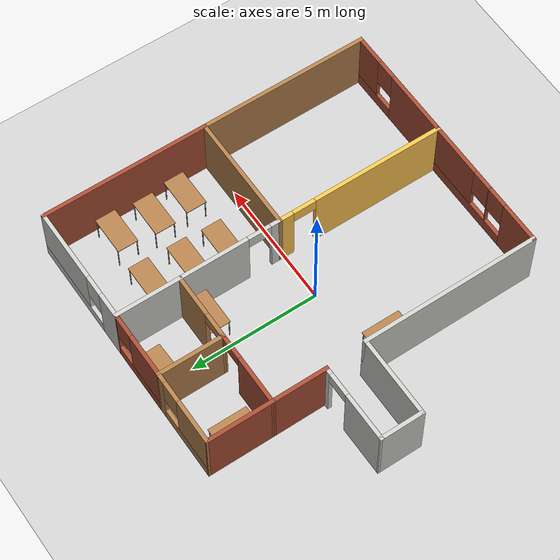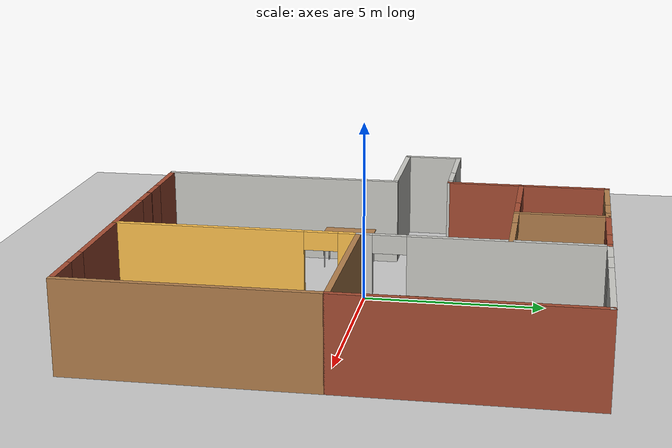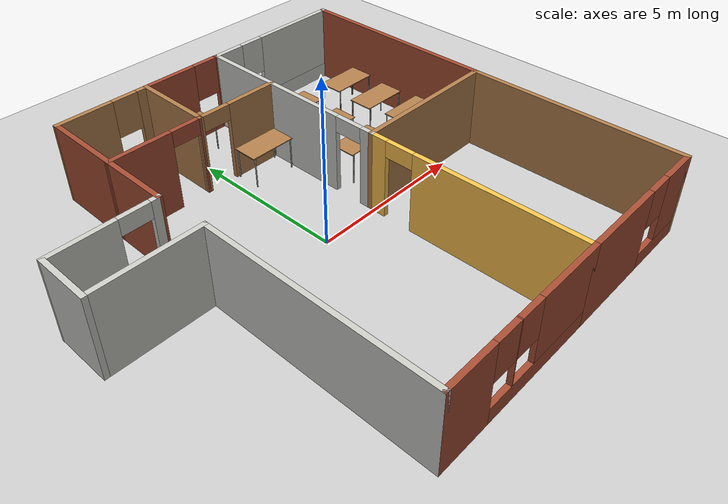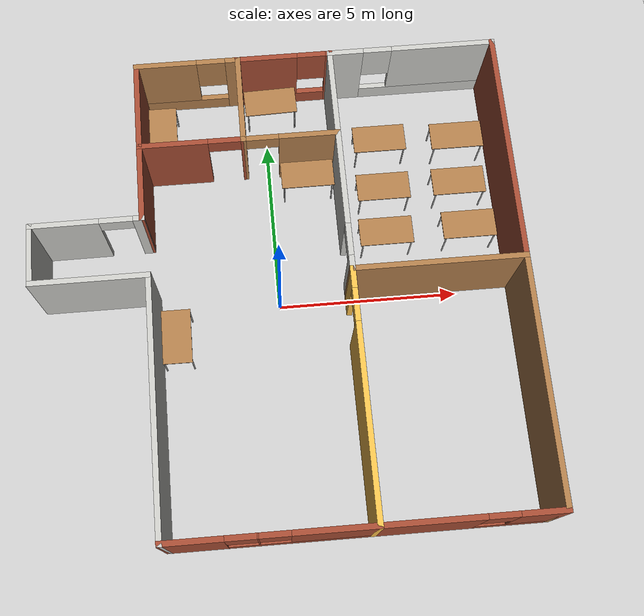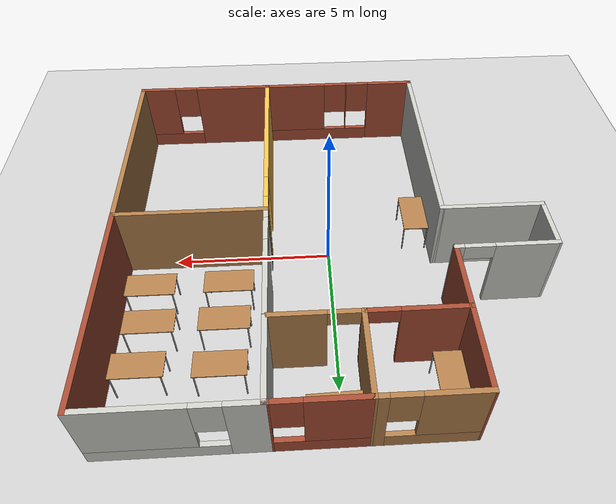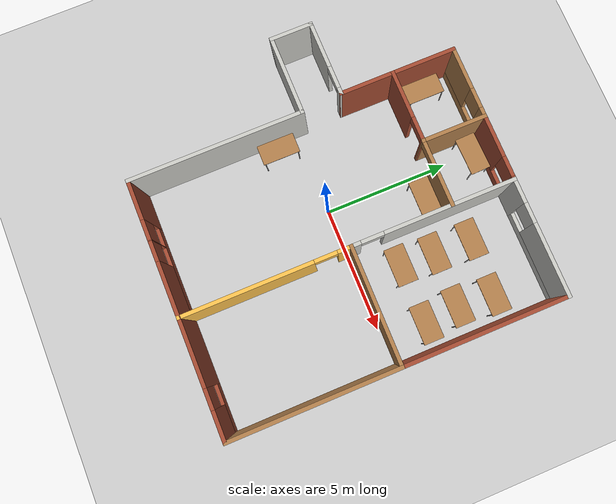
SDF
<sdf version="1.6">
 <world name="default">
  <plugin name="welcome_message" filename="libwelcome_message.so"/>
  <light name="sun" type="directional">
   <pose>0 0 10 0 -0 0</pose>
   <diffuse>0.8 0.8 0.8 1</diffuse>
   <specular>0.2 0.2 0.2 1</specular>
   <attenuation>
    <range>1000</range>
    <constant>0.9</constant>
    <linear>0.01</linear>
    <quadratic>0.001</quadratic>
   </attenuation>
   <direction>-0.5 0.1 -0.9</direction>
  </light>
  <gravity>0 0 -9.8</gravity>
  <magnetic_field>6e-06 2.3e-05 -4.2e-05</magnetic_field>
  <atmosphere type="adiabatic"/>
  <physics name="default_physics" default="0" type="ode">
   <max_step_size>0.001</max_step_size>
   <real_time_factor>1</real_time_factor>
   <real_time_update_rate>1000</real_time_update_rate>
  </physics>
  <scene><ambient>0.4 0.4 0.4 1</ambient><background>0.7 0.7 0.7 1</background><shadows>1</shadows></scene>
  <spherical_coordinates>
   <surface_model>EARTH_WGS84</surface_model>
   <latitude_deg>0</latitude_deg>
   <longitude_deg>0</longitude_deg>
   <elevation>0</elevation>
   <heading_deg>0</heading_deg>
  </spherical_coordinates>
  <model name="my_room">
   <link name="Wall_1">
    <pose>-6.52484 1.1312 0 0 0 -1.5708</pose>
    <visual name="Wall_1_Visual">
     <pose>0 0 1.25 0 -0 0</pose>
     <geometry><box><size>1.75 0.15 2.5</size></box></geometry>
     <material>
      <script><uri>file://media/materials/scripts/gazebo.material</uri><name>Gazebo/CeilingTiled</name></script>
      <ambient>1 1 1 1</ambient>
      <shader type="pixel"/>
      <diffuse>1 1 1 1</diffuse>
      <specular>0 0 0 1</specular>
      <emissive>0 0 0 1</emissive>
     </material>
     <meta><layer>0</layer></meta>
    </visual>
    <collision name="Wall_1_Collision">
     <pose>0 0 1.25 0 -0 0</pose>
     <geometry><box><size>1.75 0.15 2.5</size></box></geometry>
     <surface>
      <friction>
       <ode><mu>1</mu><mu2>1</mu2><fdir1>0 0 0</fdir1><slip1>0</slip1><slip2>0</slip2></ode>
       <torsional>
        <coefficient>1</coefficient>
        <patch_radius>0</patch_radius>
        <surface_radius>0</surface_radius>
        <use_patch_radius>1</use_patch_radius>
        <ode><slip>0</slip></ode>
       </torsional>
      </friction>
      <bounce><restitution_coefficient>0</restitution_coefficient><threshold>1e+06</threshold></bounce>
      <contact>
       <collide_without_contact>0</collide_without_contact>
       <collide_without_contact_bitmask>1</collide_without_contact_bitmask>
       <collide_bitmask>1</collide_bitmask>
       <ode>
        <soft_cfm>0</soft_cfm>
        <soft_erp>0.2</soft_erp>
        <kp>1e+13</kp>
        <kd>1</kd>
        <max_vel>0.01</max_vel>
        <min_depth>0</min_depth>
       </ode>
       <bullet>
        <split_impulse>1</split_impulse>
        <split_impulse_penetration_threshold>-0.01</split_impulse_penetration_threshold>
        <soft_cfm>0</soft_cfm>
        <soft_erp>0.2</soft_erp>
        <kp>1e+13</kp>
        <kd>1</kd>
       </bullet>
      </contact>
     </surface>
    </collision>
   </link>
   <link name="Wall_11">
    <pose>1.92516 3.29994 0 0 -0 1.5708</pose>
    <visual name="Wall_11_Visual_2">
     <pose>-2.4 0 2.25 0 -0 0</pose>
     <geometry><box><size>0.9 0.15 0.5</size></box></geometry>
     <material>
      <script><uri>file://media/materials/scripts/gazebo.material</uri><name>Gazebo/CeilingTiled</name></script>
      <ambient>0.435294 0.796078 0.67451 1</ambient>
      <shader type="pixel"/>
      <diffuse>1 1 1 1</diffuse>
      <specular>0 0 0 1</specular>
      <emissive>0 0 0 1</emissive>
     </material>
     <meta><layer>0</layer></meta>
    </visual>
    <visual name="Wall_11_Visual_1">
     <pose>0.67187 0 1.25 0 -0 0</pose>
     <geometry><box><size>5.24375 0.15 2.5</size></box></geometry>
     <material>
      <script><uri>file://media/materials/scripts/gazebo.material</uri><name>Gazebo/CeilingTiled</name></script>
      <ambient>0.435294 0.796078 0.67451 1</ambient>
      <shader type="pixel"/>
      <diffuse>1 1 1 1</diffuse>
      <specular>0 0 0 1</specular>
      <emissive>0 0 0 1</emissive>
     </material>
     <meta><layer>0</layer></meta>
    </visual>
    <visual name="Wall_11_Visual_0">
     <pose>-3.07187 0 1.25 0 -0 0</pose>
     <geometry><box><size>0.443741 0.15 2.5</size></box></geometry>
     <material>
      <script><uri>file://media/materials/scripts/gazebo.material</uri><name>Gazebo/CeilingTiled</name></script>
      <ambient>0.435294 0.796078 0.67451 1</ambient>
      <shader type="pixel"/>
      <diffuse>1 1 1 1</diffuse>
      <specular>0 0 0 1</specular>
      <emissive>0 0 0 1</emissive>
     </material>
     <meta><layer>0</layer></meta>
    </visual>
    <collision name="Wall_11_Collision_1">
     <pose>0.67187 0 1.25 0 -0 0</pose>
     <geometry><box><size>5.24375 0.15 2.5</size></box></geometry>
     <surface>
      <friction>
       <ode><mu>1</mu><mu2>1</mu2><fdir1>0 0 0</fdir1><slip1>0</slip1><slip2>0</slip2></ode>
       <torsional>
        <coefficient>1</coefficient>
        <patch_radius>0</patch_radius>
        <surface_radius>0</surface_radius>
        <use_patch_radius>1</use_patch_radius>
        <ode><slip>0</slip></ode>
       </torsional>
      </friction>
      <bounce><restitution_coefficient>0</restitution_coefficient><threshold>1e+06</threshold></bounce>
      <contact>
       <collide_without_contact>0</collide_without_contact>
       <collide_without_contact_bitmask>1</collide_without_contact_bitmask>
       <collide_bitmask>1</collide_bitmask>
       <ode>
        <soft_cfm>0</soft_cfm>
        <soft_erp>0.2</soft_erp>
        <kp>1e+13</kp>
        <kd>1</kd>
        <max_vel>0.01</max_vel>
        <min_depth>0</min_depth>
       </ode>
       <bullet>
        <split_impulse>1</split_impulse>
        <split_impulse_penetration_threshold>-0.01</split_impulse_penetration_threshold>
        <soft_cfm>0</soft_cfm>
        <soft_erp>0.2</soft_erp>
        <kp>1e+13</kp>
        <kd>1</kd>
       </bullet>
      </contact>
     </surface>
    </collision>
    <collision name="Wall_11_Collision_0">
     <pose>-3.07187 0 1.25 0 -0 0</pose>
     <geometry><box><size>0.443741 0.15 2.5</size></box></geometry>
     <surface>
      <friction>
       <ode><mu>1</mu><mu2>1</mu2><fdir1>0 0 0</fdir1><slip1>0</slip1><slip2>0</slip2></ode>
       <torsional>
        <coefficient>1</coefficient>
        <patch_radius>0</patch_radius>
        <surface_radius>0</surface_radius>
        <use_patch_radius>1</use_patch_radius>
        <ode><slip>0</slip></ode>
       </torsional>
      </friction>
      <bounce><restitution_coefficient>0</restitution_coefficient><threshold>1e+06</threshold></bounce>
      <contact>
       <collide_without_contact>0</collide_without_contact>
       <collide_without_contact_bitmask>1</collide_without_contact_bitmask>
       <collide_bitmask>1</collide_bitmask>
       <ode>
        <soft_cfm>0</soft_cfm>
        <soft_erp>0.2</soft_erp>
        <kp>1e+13</kp>
        <kd>1</kd>
        <max_vel>0.01</max_vel>
        <min_depth>0</min_depth>
       </ode>
       <bullet>
        <split_impulse>1</split_impulse>
        <split_impulse_penetration_threshold>-0.01</split_impulse_penetration_threshold>
        <soft_cfm>0</soft_cfm>
        <soft_erp>0.2</soft_erp>
        <kp>1e+13</kp>
        <kd>1</kd>
       </bullet>
      </contact>
     </surface>
    </collision>
    <collision name="Wall_11_Collision_2">
     <pose>-2.4 0 2.25 0 -0 0</pose>
     <geometry><box><size>0.9 0.15 0.5</size></box></geometry>
     <surface>
      <friction>
       <ode><mu>1</mu><mu2>1</mu2><fdir1>0 0 0</fdir1><slip1>0</slip1><slip2>0</slip2></ode>
       <torsional>
        <coefficient>1</coefficient>
        <patch_radius>0</patch_radius>
        <surface_radius>0</surface_radius>
        <use_patch_radius>1</use_patch_radius>
        <ode><slip>0</slip></ode>
       </torsional>
      </friction>
      <bounce><restitution_coefficient>0</restitution_coefficient><threshold>1e+06</threshold></bounce>
      <contact>
       <collide_without_contact>0</collide_without_contact>
       <collide_without_contact_bitmask>1</collide_without_contact_bitmask>
       <collide_bitmask>1</collide_bitmask>
       <ode>
        <soft_cfm>0</soft_cfm>
        <soft_erp>0.2</soft_erp>
        <kp>1e+13</kp>
        <kd>1</kd>
        <max_vel>0.01</max_vel>
        <min_depth>0</min_depth>
       </ode>
       <bullet>
        <split_impulse>1</split_impulse>
        <split_impulse_penetration_threshold>-0.01</split_impulse_penetration_threshold>
        <soft_cfm>0</soft_cfm>
        <soft_erp>0.2</soft_erp>
        <kp>1e+13</kp>
        <kd>1</kd>
       </bullet>
      </contact>
     </surface>
    </collision>
   </link>
   <link name="Wall_13">
    <pose>4.22516 6.51869 0 0 -0 0</pose>
    <visual name="Wall_13_Visual_0">
     <pose>-1.86124 0 1.25 0 -0 0</pose>
     <geometry><box><size>1.02753 0.15 2.5</size></box></geometry>
     <material>
      <script><uri>file://media/materials/scripts/gazebo.material</uri><name>Gazebo/CeilingTiled</name></script>
      <ambient>0.996078 0.47451 0.0196078 1</ambient>
      <shader type="pixel"/>
      <diffuse>1 1 1 1</diffuse>
      <specular>0 0 0 1</specular>
      <emissive>0 0 0 1</emissive>
     </material>
     <meta><layer>0</layer></meta>
    </visual>
    <visual name="Wall_13_Visual_3">
     <pose>-0.947474 0 1.9 0 -0 0</pose>
     <geometry><box><size>0.8 0.15 1.2</size></box></geometry>
     <material>
      <script><uri>file://media/materials/scripts/gazebo.material</uri><name>Gazebo/CeilingTiled</name></script>
      <ambient>0.996078 0.47451 0.0196078 1</ambient>
      <shader type="pixel"/>
      <diffuse>1 1 1 1</diffuse>
      <specular>0 0 0 1</specular>
      <emissive>0 0 0 1</emissive>
     </material>
     <meta><layer>0</layer></meta>
    </visual>
    <visual name="Wall_13_Visual_2">
     <pose>0.913763 0 1.5 0 -0 0</pose>
     <geometry><box><size>2.92247 0.15 2</size></box></geometry>
     <material>
      <script><uri>file://media/materials/scripts/gazebo.material</uri><name>Gazebo/CeilingTiled</name></script>
      <ambient>0.996078 0.47451 0.0196078 1</ambient>
      <shader type="pixel"/>
      <diffuse>1 1 1 1</diffuse>
      <specular>0 0 0 1</specular>
      <emissive>0 0 0 1</emissive>
     </material>
     <meta><layer>0</layer></meta>
    </visual>
    <visual name="Wall_13_Visual_1">
     <pose>0.513763 0 0.25 0 -0 0</pose>
     <geometry><box><size>3.72247 0.15 0.5</size></box></geometry>
     <material>
      <script><uri>file://media/materials/scripts/gazebo.material</uri><name>Gazebo/CeilingTiled</name></script>
      <ambient>0.996078 0.47451 0.0196078 1</ambient>
      <shader type="pixel"/>
      <diffuse>1 1 1 1</diffuse>
      <specular>0 0 0 1</specular>
      <emissive>0 0 0 1</emissive>
     </material>
     <meta><layer>0</layer></meta>
    </visual>
    <collision name="Wall_13_Collision_1">
     <pose>0.513763 0 0.25 0 -0 0</pose>
     <geometry><box><size>3.72247 0.15 0.5</size></box></geometry>
     <surface>
      <friction>
       <ode><mu>1</mu><mu2>1</mu2><fdir1>0 0 0</fdir1><slip1>0</slip1><slip2>0</slip2></ode>
       <torsional>
        <coefficient>1</coefficient>
        <patch_radius>0</patch_radius>
        <surface_radius>0</surface_radius>
        <use_patch_radius>1</use_patch_radius>
        <ode><slip>0</slip></ode>
       </torsional>
      </friction>
      <bounce><restitution_coefficient>0</restitution_coefficient><threshold>1e+06</threshold></bounce>
      <contact>
       <collide_without_contact>0</collide_without_contact>
       <collide_without_contact_bitmask>1</collide_without_contact_bitmask>
       <collide_bitmask>1</collide_bitmask>
       <ode>
        <soft_cfm>0</soft_cfm>
        <soft_erp>0.2</soft_erp>
        <kp>1e+13</kp>
        <kd>1</kd>
        <max_vel>0.01</max_vel>
        <min_depth>0</min_depth>
       </ode>
       <bullet>
        <split_impulse>1</split_impulse>
        <split_impulse_penetration_threshold>-0.01</split_impulse_penetration_threshold>
        <soft_cfm>0</soft_cfm>
        <soft_erp>0.2</soft_erp>
        <kp>1e+13</kp>
        <kd>1</kd>
       </bullet>
      </contact>
     </surface>
    </collision>
    <collision name="Wall_13_Collision_2">
     <pose>0.913763 0 1.5 0 -0 0</pose>
     <geometry><box><size>2.92247 0.15 2</size></box></geometry>
     <surface>
      <friction>
       <ode><mu>1</mu><mu2>1</mu2><fdir1>0 0 0</fdir1><slip1>0</slip1><slip2>0</slip2></ode>
       <torsional>
        <coefficient>1</coefficient>
        <patch_radius>0</patch_radius>
        <surface_radius>0</surface_radius>
        <use_patch_radius>1</use_patch_radius>
        <ode><slip>0</slip></ode>
       </torsional>
      </friction>
      <bounce><restitution_coefficient>0</restitution_coefficient><threshold>1e+06</threshold></bounce>
      <contact>
       <collide_without_contact>0</collide_without_contact>
       <collide_without_contact_bitmask>1</collide_without_contact_bitmask>
       <collide_bitmask>1</collide_bitmask>
       <ode>
        <soft_cfm>0</soft_cfm>
        <soft_erp>0.2</soft_erp>
        <kp>1e+13</kp>
        <kd>1</kd>
        <max_vel>0.01</max_vel>
        <min_depth>0</min_depth>
       </ode>
       <bullet>
        <split_impulse>1</split_impulse>
        <split_impulse_penetration_threshold>-0.01</split_impulse_penetration_threshold>
        <soft_cfm>0</soft_cfm>
        <soft_erp>0.2</soft_erp>
        <kp>1e+13</kp>
        <kd>1</kd>
       </bullet>
      </contact>
     </surface>
    </collision>
    <collision name="Wall_13_Collision_0">
     <pose>-1.86124 0 1.25 0 -0 0</pose>
     <geometry><box><size>1.02753 0.15 2.5</size></box></geometry>
     <surface>
      <friction>
       <ode><mu>1</mu><mu2>1</mu2><fdir1>0 0 0</fdir1><slip1>0</slip1><slip2>0</slip2></ode>
       <torsional>
        <coefficient>1</coefficient>
        <patch_radius>0</patch_radius>
        <surface_radius>0</surface_radius>
        <use_patch_radius>1</use_patch_radius>
        <ode><slip>0</slip></ode>
       </torsional>
      </friction>
      <bounce><restitution_coefficient>0</restitution_coefficient><threshold>1e+06</threshold></bounce>
      <contact>
       <collide_without_contact>0</collide_without_contact>
       <collide_without_contact_bitmask>1</collide_without_contact_bitmask>
       <collide_bitmask>1</collide_bitmask>
       <ode>
        <soft_cfm>0</soft_cfm>
        <soft_erp>0.2</soft_erp>
        <kp>1e+13</kp>
        <kd>1</kd>
        <max_vel>0.01</max_vel>
        <min_depth>0</min_depth>
       </ode>
       <bullet>
        <split_impulse>1</split_impulse>
        <split_impulse_penetration_threshold>-0.01</split_impulse_penetration_threshold>
        <soft_cfm>0</soft_cfm>
        <soft_erp>0.2</soft_erp>
        <kp>1e+13</kp>
        <kd>1</kd>
       </bullet>
      </contact>
     </surface>
    </collision>
    <collision name="Wall_13_Collision_3">
     <pose>-0.947474 0 1.9 0 -0 0</pose>
     <geometry><box><size>0.8 0.15 1.2</size></box></geometry>
     <surface>
      <friction>
       <ode><mu>1</mu><mu2>1</mu2><fdir1>0 0 0</fdir1><slip1>0</slip1><slip2>0</slip2></ode>
       <torsional>
        <coefficient>1</coefficient>
        <patch_radius>0</patch_radius>
        <surface_radius>0</surface_radius>
        <use_patch_radius>1</use_patch_radius>
        <ode><slip>0</slip></ode>
       </torsional>
      </friction>
      <bounce><restitution_coefficient>0</restitution_coefficient><threshold>1e+06</threshold></bounce>
      <contact>
       <collide_without_contact>0</collide_without_contact>
       <collide_without_contact_bitmask>1</collide_without_contact_bitmask>
       <collide_bitmask>1</collide_bitmask>
       <ode>
        <soft_cfm>0</soft_cfm>
        <soft_erp>0.2</soft_erp>
        <kp>1e+13</kp>
        <kd>1</kd>
        <max_vel>0.01</max_vel>
        <min_depth>0</min_depth>
       </ode>
       <bullet>
        <split_impulse>1</split_impulse>
        <split_impulse_penetration_threshold>-0.01</split_impulse_penetration_threshold>
        <soft_cfm>0</soft_cfm>
        <soft_erp>0.2</soft_erp>
        <kp>1e+13</kp>
        <kd>1</kd>
       </bullet>
      </contact>
     </surface>
    </collision>
   </link>
   <link name="Wall_14">
    <pose>6.52517 3.29994 0 0 0 -1.5708</pose>
    <visual name="Wall_14_Visual">
     <pose>0 0 1.25 0 -0 0</pose>
     <geometry><box><size>6.58749 0.15 2.5</size></box></geometry>
     <material>
      <script><uri>file://media/materials/scripts/gazebo.material</uri><name>Gazebo/Bricks</name></script>
      <ambient>1 1 1 1</ambient>
      <shader type="pixel"/>
      <diffuse>1 1 1 1</diffuse>
      <specular>0.2 0.2 0.2 1</specular>
      <emissive>0 0 0 1</emissive>
     </material>
     <meta><layer>0</layer></meta>
    </visual>
    <collision name="Wall_14_Collision">
     <pose>0 0 1.25 0 -0 0</pose>
     <geometry><box><size>6.58749 0.15 2.5</size></box></geometry>
     <surface>
      <friction>
       <ode><mu>1</mu><mu2>1</mu2><fdir1>0 0 0</fdir1><slip1>0</slip1><slip2>0</slip2></ode>
       <torsional>
        <coefficient>1</coefficient>
        <patch_radius>0</patch_radius>
        <surface_radius>0</surface_radius>
        <use_patch_radius>1</use_patch_radius>
        <ode><slip>0</slip></ode>
       </torsional>
      </friction>
      <bounce><restitution_coefficient>0</restitution_coefficient><threshold>1e+06</threshold></bounce>
      <contact>
       <collide_without_contact>0</collide_without_contact>
       <collide_without_contact_bitmask>1</collide_without_contact_bitmask>
       <collide_bitmask>1</collide_bitmask>
       <ode>
        <soft_cfm>0</soft_cfm>
        <soft_erp>0.2</soft_erp>
        <kp>1e+13</kp>
        <kd>1</kd>
        <max_vel>0.01</max_vel>
        <min_depth>0</min_depth>
       </ode>
       <bullet>
        <split_impulse>1</split_impulse>
        <split_impulse_penetration_threshold>-0.01</split_impulse_penetration_threshold>
        <soft_cfm>0</soft_cfm>
        <soft_erp>0.2</soft_erp>
        <kp>1e+13</kp>
        <kd>1</kd>
       </bullet>
      </contact>
     </surface>
    </collision>
   </link>
   <link name="Wall_16">
    <pose>0.625164 6.51869 0 0 -0 3.14159</pose>
    <visual name="Wall_16_Visual_0">
     <pose>-1.27625 0 1.25 0 -0 0</pose>
     <geometry><box><size>0.197492 0.15 2.5</size></box></geometry>
     <material>
      <script><uri>file://media/materials/scripts/gazebo.material</uri><name>Gazebo/Bricks</name></script>
      <ambient>1 1 1 1</ambient>
      <shader type="pixel"/>
      <diffuse>1 1 1 1</diffuse>
      <specular>0.2 0.2 0.2 1</specular>
      <emissive>0 0 0 1</emissive>
     </material>
     <meta><layer>0</layer></meta>
    </visual>
    <visual name="Wall_16_Visual_1">
     <pose>0.098746 0 0.25 0 -0 0</pose>
     <geometry><box><size>2.55251 0.15 0.5</size></box></geometry>
     <material>
      <script><uri>file://media/materials/scripts/gazebo.material</uri><name>Gazebo/Bricks</name></script>
      <ambient>1 1 1 1</ambient>
      <shader type="pixel"/>
      <diffuse>1 1 1 1</diffuse>
      <specular>0.2 0.2 0.2 1</specular>
      <emissive>0 0 0 1</emissive>
     </material>
     <meta><layer>0</layer></meta>
    </visual>
    <visual name="Wall_16_Visual_2">
     <pose>0.498746 0 1.5 0 -0 0</pose>
     <geometry><box><size>1.75251 0.15 2</size></box></geometry>
     <material>
      <script><uri>file://media/materials/scripts/gazebo.material</uri><name>Gazebo/Bricks</name></script>
      <ambient>1 1 1 1</ambient>
      <shader type="pixel"/>
      <diffuse>1 1 1 1</diffuse>
      <specular>0.2 0.2 0.2 1</specular>
      <emissive>0 0 0 1</emissive>
     </material>
     <meta><layer>0</layer></meta>
    </visual>
    <visual name="Wall_16_Visual_3">
     <pose>-0.777508 0 1.9 0 -0 0</pose>
     <geometry><box><size>0.8 0.15 1.2</size></box></geometry>
     <material>
      <script><uri>file://media/materials/scripts/gazebo.material</uri><name>Gazebo/Bricks</name></script>
      <ambient>1 1 1 1</ambient>
      <shader type="pixel"/>
      <diffuse>1 1 1 1</diffuse>
      <specular>0.2 0.2 0.2 1</specular>
      <emissive>0 0 0 1</emissive>
     </material>
     <meta><layer>0</layer></meta>
    </visual>
    <collision name="Wall_16_Collision_0">
     <pose>-1.27625 0 1.25 0 -0 0</pose>
     <geometry><box><size>0.197492 0.15 2.5</size></box></geometry>
     <surface>
      <friction>
       <ode><mu>1</mu><mu2>1</mu2><fdir1>0 0 0</fdir1><slip1>0</slip1><slip2>0</slip2></ode>
       <torsional>
        <coefficient>1</coefficient>
        <patch_radius>0</patch_radius>
        <surface_radius>0</surface_radius>
        <use_patch_radius>1</use_patch_radius>
        <ode><slip>0</slip></ode>
       </torsional>
      </friction>
      <bounce><restitution_coefficient>0</restitution_coefficient><threshold>1e+06</threshold></bounce>
      <contact>
       <collide_without_contact>0</collide_without_contact>
       <collide_without_contact_bitmask>1</collide_without_contact_bitmask>
       <collide_bitmask>1</collide_bitmask>
       <ode>
        <soft_cfm>0</soft_cfm>
        <soft_erp>0.2</soft_erp>
        <kp>1e+13</kp>
        <kd>1</kd>
        <max_vel>0.01</max_vel>
        <min_depth>0</min_depth>
       </ode>
       <bullet>
        <split_impulse>1</split_impulse>
        <split_impulse_penetration_threshold>-0.01</split_impulse_penetration_threshold>
        <soft_cfm>0</soft_cfm>
        <soft_erp>0.2</soft_erp>
        <kp>1e+13</kp>
        <kd>1</kd>
       </bullet>
      </contact>
     </surface>
    </collision>
    <collision name="Wall_16_Collision_2">
     <pose>0.498746 0 1.5 0 -0 0</pose>
     <geometry><box><size>1.75251 0.15 2</size></box></geometry>
     <surface>
      <friction>
       <ode><mu>1</mu><mu2>1</mu2><fdir1>0 0 0</fdir1><slip1>0</slip1><slip2>0</slip2></ode>
       <torsional>
        <coefficient>1</coefficient>
        <patch_radius>0</patch_radius>
        <surface_radius>0</surface_radius>
        <use_patch_radius>1</use_patch_radius>
        <ode><slip>0</slip></ode>
       </torsional>
      </friction>
      <bounce><restitution_coefficient>0</restitution_coefficient><threshold>1e+06</threshold></bounce>
      <contact>
       <collide_without_contact>0</collide_without_contact>
       <collide_without_contact_bitmask>1</collide_without_contact_bitmask>
       <collide_bitmask>1</collide_bitmask>
       <ode>
        <soft_cfm>0</soft_cfm>
        <soft_erp>0.2</soft_erp>
        <kp>1e+13</kp>
        <kd>1</kd>
        <max_vel>0.01</max_vel>
        <min_depth>0</min_depth>
       </ode>
       <bullet>
        <split_impulse>1</split_impulse>
        <split_impulse_penetration_threshold>-0.01</split_impulse_penetration_threshold>
        <soft_cfm>0</soft_cfm>
        <soft_erp>0.2</soft_erp>
        <kp>1e+13</kp>
        <kd>1</kd>
       </bullet>
      </contact>
     </surface>
    </collision>
    <collision name="Wall_16_Collision_1">
     <pose>0.098746 0 0.25 0 -0 0</pose>
     <geometry><box><size>2.55251 0.15 0.5</size></box></geometry>
     <surface>
      <friction>
       <ode><mu>1</mu><mu2>1</mu2><fdir1>0 0 0</fdir1><slip1>0</slip1><slip2>0</slip2></ode>
       <torsional>
        <coefficient>1</coefficient>
        <patch_radius>0</patch_radius>
        <surface_radius>0</surface_radius>
        <use_patch_radius>1</use_patch_radius>
        <ode><slip>0</slip></ode>
       </torsional>
      </friction>
      <bounce><restitution_coefficient>0</restitution_coefficient><threshold>1e+06</threshold></bounce>
      <contact>
       <collide_without_contact>0</collide_without_contact>
       <collide_without_contact_bitmask>1</collide_without_contact_bitmask>
       <collide_bitmask>1</collide_bitmask>
       <ode>
        <soft_cfm>0</soft_cfm>
        <soft_erp>0.2</soft_erp>
        <kp>1e+13</kp>
        <kd>1</kd>
        <max_vel>0.01</max_vel>
        <min_depth>0</min_depth>
       </ode>
       <bullet>
        <split_impulse>1</split_impulse>
        <split_impulse_penetration_threshold>-0.01</split_impulse_penetration_threshold>
        <soft_cfm>0</soft_cfm>
        <soft_erp>0.2</soft_erp>
        <kp>1e+13</kp>
        <kd>1</kd>
       </bullet>
      </contact>
     </surface>
    </collision>
    <collision name="Wall_16_Collision_3">
     <pose>-0.777508 0 1.9 0 -0 0</pose>
     <geometry><box><size>0.8 0.15 1.2</size></box></geometry>
     <surface>
      <friction>
       <ode><mu>1</mu><mu2>1</mu2><fdir1>0 0 0</fdir1><slip1>0</slip1><slip2>0</slip2></ode>
       <torsional>
        <coefficient>1</coefficient>
        <patch_radius>0</patch_radius>
        <surface_radius>0</surface_radius>
        <use_patch_radius>1</use_patch_radius>
        <ode><slip>0</slip></ode>
       </torsional>
      </friction>
      <bounce><restitution_coefficient>0</restitution_coefficient><threshold>1e+06</threshold></bounce>
      <contact>
       <collide_without_contact>0</collide_without_contact>
       <collide_without_contact_bitmask>1</collide_without_contact_bitmask>
       <collide_bitmask>1</collide_bitmask>
       <ode>
        <soft_cfm>0</soft_cfm>
        <soft_erp>0.2</soft_erp>
        <kp>1e+13</kp>
        <kd>1</kd>
        <max_vel>0.01</max_vel>
        <min_depth>0</min_depth>
       </ode>
       <bullet>
        <split_impulse>1</split_impulse>
        <split_impulse_penetration_threshold>-0.01</split_impulse_penetration_threshold>
        <soft_cfm>0</soft_cfm>
        <soft_erp>0.2</soft_erp>
        <kp>1e+13</kp>
        <kd>1</kd>
       </bullet>
      </contact>
     </surface>
    </collision>
   </link>
   <link name="Wall_2">
    <pose>-4.97483 0.3312 0 0 -0 0</pose>
    <visual name="Wall_2_Visual">
     <pose>0 0 1.25 0 -0 0</pose>
     <geometry><box><size>3.25 0.15 2.5</size></box></geometry>
     <material>
      <script><uri>file://media/materials/scripts/gazebo.material</uri><name>Gazebo/CeilingTiled</name></script>
      <ambient>1 1 1 1</ambient>
      <shader type="pixel"/>
      <diffuse>1 1 1 1</diffuse>
      <specular>0 0 0 1</specular>
      <emissive>0 0 0 1</emissive>
     </material>
     <meta><layer>0</layer></meta>
    </visual>
    <collision name="Wall_2_Collision">
     <pose>0 0 1.25 0 -0 0</pose>
     <geometry><box><size>3.25 0.15 2.5</size></box></geometry>
     <surface>
      <friction>
       <ode><mu>1</mu><mu2>1</mu2><fdir1>0 0 0</fdir1><slip1>0</slip1><slip2>0</slip2></ode>
       <torsional>
        <coefficient>1</coefficient>
        <patch_radius>0</patch_radius>
        <surface_radius>0</surface_radius>
        <use_patch_radius>1</use_patch_radius>
        <ode><slip>0</slip></ode>
       </torsional>
      </friction>
      <bounce><restitution_coefficient>0</restitution_coefficient><threshold>1e+06</threshold></bounce>
      <contact>
       <collide_without_contact>0</collide_without_contact>
       <collide_without_contact_bitmask>1</collide_without_contact_bitmask>
       <collide_bitmask>1</collide_bitmask>
       <ode>
        <soft_cfm>0</soft_cfm>
        <soft_erp>0.2</soft_erp>
        <kp>1e+13</kp>
        <kd>1</kd>
        <max_vel>0.01</max_vel>
        <min_depth>0</min_depth>
       </ode>
       <bullet>
        <split_impulse>1</split_impulse>
        <split_impulse_penetration_threshold>-0.01</split_impulse_penetration_threshold>
        <soft_cfm>0</soft_cfm>
        <soft_erp>0.2</soft_erp>
        <kp>1e+13</kp>
        <kd>1</kd>
       </bullet>
      </contact>
     </surface>
    </collision>
   </link>
   <link name="Wall_26">
    <pose>0.621451 4.04438 0 0 -0 3.14159</pose>
    <visual name="Wall_26_Visual_2">
     <pose>0.778216 0 2.25 0 -0 0</pose>
     <geometry><box><size>0.9 0.15 0.5</size></box></geometry>
     <material>
      <script><uri>file://media/materials/scripts/gazebo.material</uri><name>Gazebo/Wood</name></script>
      <ambient>1 1 1 1</ambient>
      <shader type="pixel"/>
      <diffuse>1 1 1 1</diffuse>
      <specular>0.2 0.2 0.2 1</specular>
      <emissive>0 0 0 1</emissive>
     </material>
     <meta><layer>0</layer></meta>
    </visual>
    <visual name="Wall_26_Visual_1">
     <pose>1.30161 0 1.25 0 -0 0</pose>
     <geometry><box><size>0.146784 0.15 2.5</size></box></geometry>
     <material>
      <script><uri>file://media/materials/scripts/gazebo.material</uri><name>Gazebo/Wood</name></script>
      <ambient>1 1 1 1</ambient>
      <shader type="pixel"/>
      <diffuse>1 1 1 1</diffuse>
      <specular>0.2 0.2 0.2 1</specular>
      <emissive>0 0 0 1</emissive>
     </material>
     <meta><layer>0</layer></meta>
    </visual>
    <visual name="Wall_26_Visual_0">
     <pose>-0.523392 0 1.25 0 -0 0</pose>
     <geometry><box><size>1.70322 0.15 2.5</size></box></geometry>
     <material>
      <script><uri>file://media/materials/scripts/gazebo.material</uri><name>Gazebo/Wood</name></script>
      <ambient>1 1 1 1</ambient>
      <shader type="pixel"/>
      <diffuse>1 1 1 1</diffuse>
      <specular>0.2 0.2 0.2 1</specular>
      <emissive>0 0 0 1</emissive>
     </material>
     <meta><layer>0</layer></meta>
    </visual>
    <collision name="Wall_26_Collision_0">
     <pose>-0.523392 0 1.25 0 -0 0</pose>
     <geometry><box><size>1.70322 0.15 2.5</size></box></geometry>
     <surface>
      <friction>
       <ode><mu>1</mu><mu2>1</mu2><fdir1>0 0 0</fdir1><slip1>0</slip1><slip2>0</slip2></ode>
       <torsional>
        <coefficient>1</coefficient>
        <patch_radius>0</patch_radius>
        <surface_radius>0</surface_radius>
        <use_patch_radius>1</use_patch_radius>
        <ode><slip>0</slip></ode>
       </torsional>
      </friction>
      <bounce><restitution_coefficient>0</restitution_coefficient><threshold>1e+06</threshold></bounce>
      <contact>
       <collide_without_contact>0</collide_without_contact>
       <collide_without_contact_bitmask>1</collide_without_contact_bitmask>
       <collide_bitmask>1</collide_bitmask>
       <ode>
        <soft_cfm>0</soft_cfm>
        <soft_erp>0.2</soft_erp>
        <kp>1e+13</kp>
        <kd>1</kd>
        <max_vel>0.01</max_vel>
        <min_depth>0</min_depth>
       </ode>
       <bullet>
        <split_impulse>1</split_impulse>
        <split_impulse_penetration_threshold>-0.01</split_impulse_penetration_threshold>
        <soft_cfm>0</soft_cfm>
        <soft_erp>0.2</soft_erp>
        <kp>1e+13</kp>
        <kd>1</kd>
       </bullet>
      </contact>
     </surface>
    </collision>
    <collision name="Wall_26_Collision_1">
     <pose>1.30161 0 1.25 0 -0 0</pose>
     <geometry><box><size>0.146784 0.15 2.5</size></box></geometry>
     <surface>
      <friction>
       <ode><mu>1</mu><mu2>1</mu2><fdir1>0 0 0</fdir1><slip1>0</slip1><slip2>0</slip2></ode>
       <torsional>
        <coefficient>1</coefficient>
        <patch_radius>0</patch_radius>
        <surface_radius>0</surface_radius>
        <use_patch_radius>1</use_patch_radius>
        <ode><slip>0</slip></ode>
       </torsional>
      </friction>
      <bounce><restitution_coefficient>0</restitution_coefficient><threshold>1e+06</threshold></bounce>
      <contact>
       <collide_without_contact>0</collide_without_contact>
       <collide_without_contact_bitmask>1</collide_without_contact_bitmask>
       <collide_bitmask>1</collide_bitmask>
       <ode>
        <soft_cfm>0</soft_cfm>
        <soft_erp>0.2</soft_erp>
        <kp>1e+13</kp>
        <kd>1</kd>
        <max_vel>0.01</max_vel>
        <min_depth>0</min_depth>
       </ode>
       <bullet>
        <split_impulse>1</split_impulse>
        <split_impulse_penetration_threshold>-0.01</split_impulse_penetration_threshold>
        <soft_cfm>0</soft_cfm>
        <soft_erp>0.2</soft_erp>
        <kp>1e+13</kp>
        <kd>1</kd>
       </bullet>
      </contact>
     </surface>
    </collision>
    <collision name="Wall_26_Collision_2">
     <pose>0.778216 0 2.25 0 -0 0</pose>
     <geometry><box><size>0.9 0.15 0.5</size></box></geometry>
     <surface>
      <friction>
       <ode><mu>1</mu><mu2>1</mu2><fdir1>0 0 0</fdir1><slip1>0</slip1><slip2>0</slip2></ode>
       <torsional>
        <coefficient>1</coefficient>
        <patch_radius>0</patch_radius>
        <surface_radius>0</surface_radius>
        <use_patch_radius>1</use_patch_radius>
        <ode><slip>0</slip></ode>
       </torsional>
      </friction>
      <bounce><restitution_coefficient>0</restitution_coefficient><threshold>1e+06</threshold></bounce>
      <contact>
       <collide_without_contact>0</collide_without_contact>
       <collide_without_contact_bitmask>1</collide_without_contact_bitmask>
       <collide_bitmask>1</collide_bitmask>
       <ode>
        <soft_cfm>0</soft_cfm>
        <soft_erp>0.2</soft_erp>
        <kp>1e+13</kp>
        <kd>1</kd>
        <max_vel>0.01</max_vel>
        <min_depth>0</min_depth>
       </ode>
       <bullet>
        <split_impulse>1</split_impulse>
        <split_impulse_penetration_threshold>-0.01</split_impulse_penetration_threshold>
        <soft_cfm>0</soft_cfm>
        <soft_erp>0.2</soft_erp>
        <kp>1e+13</kp>
        <kd>1</kd>
       </bullet>
      </contact>
     </surface>
    </collision>
   </link>
   <link name="Wall_27">
    <pose>-2.10355 4.04438 0 0 -0 3.14159</pose>
    <visual name="Wall_27_Visual_1">
     <pose>0.523887 0 1.25 0 -0 0</pose>
     <geometry><box><size>1.95223 0.15 2.5</size></box></geometry>
     <material>
      <script><uri>file://media/materials/scripts/gazebo.material</uri><name>Gazebo/Bricks</name></script>
      <ambient>1 1 1 1</ambient>
      <shader type="pixel"/>
      <diffuse>1 1 1 1</diffuse>
      <specular>0.2 0.2 0.2 1</specular>
      <emissive>0 0 0 1</emissive>
     </material>
     <meta><layer>0</layer></meta>
    </visual>
    <visual name="Wall_27_Visual_2">
     <pose>-0.902225 0 2.25 0 -0 0</pose>
     <geometry><box><size>0.9 0.15 0.5</size></box></geometry>
     <material>
      <script><uri>file://media/materials/scripts/gazebo.material</uri><name>Gazebo/Bricks</name></script>
      <ambient>1 1 1 1</ambient>
      <shader type="pixel"/>
      <diffuse>1 1 1 1</diffuse>
      <specular>0.2 0.2 0.2 1</specular>
      <emissive>0 0 0 1</emissive>
     </material>
     <meta><layer>0</layer></meta>
    </visual>
    <visual name="Wall_27_Visual_0">
     <pose>-1.42611 0 1.25 0 -0 0</pose>
     <geometry><box><size>0.147775 0.15 2.5</size></box></geometry>
     <material>
      <script><uri>file://media/materials/scripts/gazebo.material</uri><name>Gazebo/Bricks</name></script>
      <ambient>1 1 1 1</ambient>
      <shader type="pixel"/>
      <diffuse>1 1 1 1</diffuse>
      <specular>0.2 0.2 0.2 1</specular>
      <emissive>0 0 0 1</emissive>
     </material>
     <meta><layer>0</layer></meta>
    </visual>
    <collision name="Wall_27_Collision_2">
     <pose>-0.902225 0 2.25 0 -0 0</pose>
     <geometry><box><size>0.9 0.15 0.5</size></box></geometry>
     <surface>
      <friction>
       <ode><mu>1</mu><mu2>1</mu2><fdir1>0 0 0</fdir1><slip1>0</slip1><slip2>0</slip2></ode>
       <torsional>
        <coefficient>1</coefficient>
        <patch_radius>0</patch_radius>
        <surface_radius>0</surface_radius>
        <use_patch_radius>1</use_patch_radius>
        <ode><slip>0</slip></ode>
       </torsional>
      </friction>
      <bounce><restitution_coefficient>0</restitution_coefficient><threshold>1e+06</threshold></bounce>
      <contact>
       <collide_without_contact>0</collide_without_contact>
       <collide_without_contact_bitmask>1</collide_without_contact_bitmask>
       <collide_bitmask>1</collide_bitmask>
       <ode>
        <soft_cfm>0</soft_cfm>
        <soft_erp>0.2</soft_erp>
        <kp>1e+13</kp>
        <kd>1</kd>
        <max_vel>0.01</max_vel>
        <min_depth>0</min_depth>
       </ode>
       <bullet>
        <split_impulse>1</split_impulse>
        <split_impulse_penetration_threshold>-0.01</split_impulse_penetration_threshold>
        <soft_cfm>0</soft_cfm>
        <soft_erp>0.2</soft_erp>
        <kp>1e+13</kp>
        <kd>1</kd>
       </bullet>
      </contact>
     </surface>
    </collision>
    <collision name="Wall_27_Collision_1">
     <pose>0.523887 0 1.25 0 -0 0</pose>
     <geometry><box><size>1.95223 0.15 2.5</size></box></geometry>
     <surface>
      <friction>
       <ode><mu>1</mu><mu2>1</mu2><fdir1>0 0 0</fdir1><slip1>0</slip1><slip2>0</slip2></ode>
       <torsional>
        <coefficient>1</coefficient>
        <patch_radius>0</patch_radius>
        <surface_radius>0</surface_radius>
        <use_patch_radius>1</use_patch_radius>
        <ode><slip>0</slip></ode>
       </torsional>
      </friction>
      <bounce><restitution_coefficient>0</restitution_coefficient><threshold>1e+06</threshold></bounce>
      <contact>
       <collide_without_contact>0</collide_without_contact>
       <collide_without_contact_bitmask>1</collide_without_contact_bitmask>
       <collide_bitmask>1</collide_bitmask>
       <ode>
        <soft_cfm>0</soft_cfm>
        <soft_erp>0.2</soft_erp>
        <kp>1e+13</kp>
        <kd>1</kd>
        <max_vel>0.01</max_vel>
        <min_depth>0</min_depth>
       </ode>
       <bullet>
        <split_impulse>1</split_impulse>
        <split_impulse_penetration_threshold>-0.01</split_impulse_penetration_threshold>
        <soft_cfm>0</soft_cfm>
        <soft_erp>0.2</soft_erp>
        <kp>1e+13</kp>
        <kd>1</kd>
       </bullet>
      </contact>
     </surface>
    </collision>
    <collision name="Wall_27_Collision_0">
     <pose>-1.42611 0 1.25 0 -0 0</pose>
     <geometry><box><size>0.147775 0.15 2.5</size></box></geometry>
     <surface>
      <friction>
       <ode><mu>1</mu><mu2>1</mu2><fdir1>0 0 0</fdir1><slip1>0</slip1><slip2>0</slip2></ode>
       <torsional>
        <coefficient>1</coefficient>
        <patch_radius>0</patch_radius>
        <surface_radius>0</surface_radius>
        <use_patch_radius>1</use_patch_radius>
        <ode><slip>0</slip></ode>
       </torsional>
      </friction>
      <bounce><restitution_coefficient>0</restitution_coefficient><threshold>1e+06</threshold></bounce>
      <contact>
       <collide_without_contact>0</collide_without_contact>
       <collide_without_contact_bitmask>1</collide_without_contact_bitmask>
       <collide_bitmask>1</collide_bitmask>
       <ode>
        <soft_cfm>0</soft_cfm>
        <soft_erp>0.2</soft_erp>
        <kp>1e+13</kp>
        <kd>1</kd>
        <max_vel>0.01</max_vel>
        <min_depth>0</min_depth>
       </ode>
       <bullet>
        <split_impulse>1</split_impulse>
        <split_impulse_penetration_threshold>-0.01</split_impulse_penetration_threshold>
        <soft_cfm>0</soft_cfm>
        <soft_erp>0.2</soft_erp>
        <kp>1e+13</kp>
        <kd>1</kd>
       </bullet>
      </contact>
     </surface>
    </collision>
   </link>
   <link name="Wall_3">
    <pose>-3.42483 -3.0938 0 0 0 -1.5708</pose>
    <visual name="Wall_3_Visual">
     <pose>0 0 1.25 0 -0 0</pose>
     <geometry><box><size>7 0.15 2.5</size></box></geometry>
     <material>
      <script><uri>file://media/materials/scripts/gazebo.material</uri><name>Gazebo/CeilingTiled</name></script>
      <ambient>0.760784 0.662745 0.627451 1</ambient>
      <shader type="pixel"/>
      <diffuse>1 1 1 1</diffuse>
      <specular>0 0 0 1</specular>
      <emissive>0 0 0 1</emissive>
     </material>
     <meta><layer>0</layer></meta>
    </visual>
    <collision name="Wall_3_Collision">
     <pose>0 0 1.25 0 -0 0</pose>
     <geometry><box><size>7 0.15 2.5</size></box></geometry>
     <surface>
      <friction>
       <ode><mu>1</mu><mu2>1</mu2><fdir1>0 0 0</fdir1><slip1>0</slip1><slip2>0</slip2></ode>
       <torsional>
        <coefficient>1</coefficient>
        <patch_radius>0</patch_radius>
        <surface_radius>0</surface_radius>
        <use_patch_radius>1</use_patch_radius>
        <ode><slip>0</slip></ode>
       </torsional>
      </friction>
      <bounce><restitution_coefficient>0</restitution_coefficient><threshold>1e+06</threshold></bounce>
      <contact>
       <collide_without_contact>0</collide_without_contact>
       <collide_without_contact_bitmask>1</collide_without_contact_bitmask>
       <collide_bitmask>1</collide_bitmask>
       <ode>
        <soft_cfm>0</soft_cfm>
        <soft_erp>0.2</soft_erp>
        <kp>1e+13</kp>
        <kd>1</kd>
        <max_vel>0.01</max_vel>
        <min_depth>0</min_depth>
       </ode>
       <bullet>
        <split_impulse>1</split_impulse>
        <split_impulse_penetration_threshold>-0.01</split_impulse_penetration_threshold>
        <soft_cfm>0</soft_cfm>
        <soft_erp>0.2</soft_erp>
        <kp>1e+13</kp>
        <kd>1</kd>
       </bullet>
      </contact>
     </surface>
    </collision>
   </link>
   <link name="Wall_30">
    <pose>-2.09984 6.51869 0 0 -0 3.14159</pose>
    <visual name="Wall_30_Visual_0">
     <pose>-1.28297 0 1.25 0 -0 0</pose>
     <geometry><box><size>0.434056 0.15 2.5</size></box></geometry>
     <material>
      <script><uri>file://media/materials/scripts/gazebo.material</uri><name>Gazebo/Wood</name></script>
      <ambient>1 1 1 1</ambient>
      <shader type="pixel"/>
      <diffuse>1 1 1 1</diffuse>
      <specular>0.2 0.2 0.2 1</specular>
      <emissive>0 0 0 1</emissive>
     </material>
     <meta><layer>0</layer></meta>
    </visual>
    <visual name="Wall_30_Visual_1">
     <pose>0.217028 0 0.25 0 -0 0</pose>
     <geometry><box><size>2.56594 0.15 0.5</size></box></geometry>
     <material>
      <script><uri>file://media/materials/scripts/gazebo.material</uri><name>Gazebo/Wood</name></script>
      <ambient>1 1 1 1</ambient>
      <shader type="pixel"/>
      <diffuse>1 1 1 1</diffuse>
      <specular>0.2 0.2 0.2 1</specular>
      <emissive>0 0 0 1</emissive>
     </material>
     <meta><layer>0</layer></meta>
    </visual>
    <visual name="Wall_30_Visual_3">
     <pose>-0.665944 0 1.9 0 -0 0</pose>
     <geometry><box><size>0.8 0.15 1.2</size></box></geometry>
     <material>
      <script><uri>file://media/materials/scripts/gazebo.material</uri><name>Gazebo/Wood</name></script>
      <ambient>1 1 1 1</ambient>
      <shader type="pixel"/>
      <diffuse>1 1 1 1</diffuse>
      <specular>0.2 0.2 0.2 1</specular>
      <emissive>0 0 0 1</emissive>
     </material>
     <meta><layer>0</layer></meta>
    </visual>
    <visual name="Wall_30_Visual_2">
     <pose>0.617028 0 1.5 0 -0 0</pose>
     <geometry><box><size>1.76594 0.15 2</size></box></geometry>
     <material>
      <script><uri>file://media/materials/scripts/gazebo.material</uri><name>Gazebo/Wood</name></script>
      <ambient>1 1 1 1</ambient>
      <shader type="pixel"/>
      <diffuse>1 1 1 1</diffuse>
      <specular>0.2 0.2 0.2 1</specular>
      <emissive>0 0 0 1</emissive>
     </material>
     <meta><layer>0</layer></meta>
    </visual>
    <collision name="Wall_30_Collision_1">
     <pose>0.217028 0 0.25 0 -0 0</pose>
     <geometry><box><size>2.56594 0.15 0.5</size></box></geometry>
     <surface>
      <friction>
       <ode><mu>1</mu><mu2>1</mu2><fdir1>0 0 0</fdir1><slip1>0</slip1><slip2>0</slip2></ode>
       <torsional>
        <coefficient>1</coefficient>
        <patch_radius>0</patch_radius>
        <surface_radius>0</surface_radius>
        <use_patch_radius>1</use_patch_radius>
        <ode><slip>0</slip></ode>
       </torsional>
      </friction>
      <bounce><restitution_coefficient>0</restitution_coefficient><threshold>1e+06</threshold></bounce>
      <contact>
       <collide_without_contact>0</collide_without_contact>
       <collide_without_contact_bitmask>1</collide_without_contact_bitmask>
       <collide_bitmask>1</collide_bitmask>
       <ode>
        <soft_cfm>0</soft_cfm>
        <soft_erp>0.2</soft_erp>
        <kp>1e+13</kp>
        <kd>1</kd>
        <max_vel>0.01</max_vel>
        <min_depth>0</min_depth>
       </ode>
       <bullet>
        <split_impulse>1</split_impulse>
        <split_impulse_penetration_threshold>-0.01</split_impulse_penetration_threshold>
        <soft_cfm>0</soft_cfm>
        <soft_erp>0.2</soft_erp>
        <kp>1e+13</kp>
        <kd>1</kd>
       </bullet>
      </contact>
     </surface>
    </collision>
    <collision name="Wall_30_Collision_2">
     <pose>0.617028 0 1.5 0 -0 0</pose>
     <geometry><box><size>1.76594 0.15 2</size></box></geometry>
     <surface>
      <friction>
       <ode><mu>1</mu><mu2>1</mu2><fdir1>0 0 0</fdir1><slip1>0</slip1><slip2>0</slip2></ode>
       <torsional>
        <coefficient>1</coefficient>
        <patch_radius>0</patch_radius>
        <surface_radius>0</surface_radius>
        <use_patch_radius>1</use_patch_radius>
        <ode><slip>0</slip></ode>
       </torsional>
      </friction>
      <bounce><restitution_coefficient>0</restitution_coefficient><threshold>1e+06</threshold></bounce>
      <contact>
       <collide_without_contact>0</collide_without_contact>
       <collide_without_contact_bitmask>1</collide_without_contact_bitmask>
       <collide_bitmask>1</collide_bitmask>
       <ode>
        <soft_cfm>0</soft_cfm>
        <soft_erp>0.2</soft_erp>
        <kp>1e+13</kp>
        <kd>1</kd>
        <max_vel>0.01</max_vel>
        <min_depth>0</min_depth>
       </ode>
       <bullet>
        <split_impulse>1</split_impulse>
        <split_impulse_penetration_threshold>-0.01</split_impulse_penetration_threshold>
        <soft_cfm>0</soft_cfm>
        <soft_erp>0.2</soft_erp>
        <kp>1e+13</kp>
        <kd>1</kd>
       </bullet>
      </contact>
     </surface>
    </collision>
    <collision name="Wall_30_Collision_0">
     <pose>-1.28297 0 1.25 0 -0 0</pose>
     <geometry><box><size>0.434056 0.15 2.5</size></box></geometry>
     <surface>
      <friction>
       <ode><mu>1</mu><mu2>1</mu2><fdir1>0 0 0</fdir1><slip1>0</slip1><slip2>0</slip2></ode>
       <torsional>
        <coefficient>1</coefficient>
        <patch_radius>0</patch_radius>
        <surface_radius>0</surface_radius>
        <use_patch_radius>1</use_patch_radius>
        <ode><slip>0</slip></ode>
       </torsional>
      </friction>
      <bounce><restitution_coefficient>0</restitution_coefficient><threshold>1e+06</threshold></bounce>
      <contact>
       <collide_without_contact>0</collide_without_contact>
       <collide_without_contact_bitmask>1</collide_without_contact_bitmask>
       <collide_bitmask>1</collide_bitmask>
       <ode>
        <soft_cfm>0</soft_cfm>
        <soft_erp>0.2</soft_erp>
        <kp>1e+13</kp>
        <kd>1</kd>
        <max_vel>0.01</max_vel>
        <min_depth>0</min_depth>
       </ode>
       <bullet>
        <split_impulse>1</split_impulse>
        <split_impulse_penetration_threshold>-0.01</split_impulse_penetration_threshold>
        <soft_cfm>0</soft_cfm>
        <soft_erp>0.2</soft_erp>
        <kp>1e+13</kp>
        <kd>1</kd>
       </bullet>
      </contact>
     </surface>
    </collision>
    <collision name="Wall_30_Collision_3">
     <pose>-0.665944 0 1.9 0 -0 0</pose>
     <geometry><box><size>0.8 0.15 1.2</size></box></geometry>
     <surface>
      <friction>
       <ode><mu>1</mu><mu2>1</mu2><fdir1>0 0 0</fdir1><slip1>0</slip1><slip2>0</slip2></ode>
       <torsional>
        <coefficient>1</coefficient>
        <patch_radius>0</patch_radius>
        <surface_radius>0</surface_radius>
        <use_patch_radius>1</use_patch_radius>
        <ode><slip>0</slip></ode>
       </torsional>
      </friction>
      <bounce><restitution_coefficient>0</restitution_coefficient><threshold>1e+06</threshold></bounce>
      <contact>
       <collide_without_contact>0</collide_without_contact>
       <collide_without_contact_bitmask>1</collide_without_contact_bitmask>
       <collide_bitmask>1</collide_bitmask>
       <ode>
        <soft_cfm>0</soft_cfm>
        <soft_erp>0.2</soft_erp>
        <kp>1e+13</kp>
        <kd>1</kd>
        <max_vel>0.01</max_vel>
        <min_depth>0</min_depth>
       </ode>
       <bullet>
        <split_impulse>1</split_impulse>
        <split_impulse_penetration_threshold>-0.01</split_impulse_penetration_threshold>
        <soft_cfm>0</soft_cfm>
        <soft_erp>0.2</soft_erp>
        <kp>1e+13</kp>
        <kd>1</kd>
       </bullet>
      </contact>
     </surface>
    </collision>
   </link>
   <link name="Wall_31">
    <pose>-3.52669 5.28153 0 0 0 -1.5723</pose>
    <visual name="Wall_31_Visual">
     <pose>0 0 1.25 0 -0 0</pose>
     <geometry><box><size>2.62431 0.15 2.5</size></box></geometry>
     <material>
      <script><uri>file://media/materials/scripts/gazebo.material</uri><name>Gazebo/Bricks</name></script>
      <ambient>1 1 1 1</ambient>
      <shader type="pixel"/>
      <diffuse>1 1 1 1</diffuse>
      <specular>0.2 0.2 0.2 1</specular>
      <emissive>0 0 0 1</emissive>
     </material>
     <meta><layer>0</layer></meta>
    </visual>
    <collision name="Wall_31_Collision">
     <pose>0 0 1.25 0 -0 0</pose>
     <geometry><box><size>2.62431 0.15 2.5</size></box></geometry>
     <surface>
      <friction>
       <ode><mu>1</mu><mu2>1</mu2><fdir1>0 0 0</fdir1><slip1>0</slip1><slip2>0</slip2></ode>
       <torsional>
        <coefficient>1</coefficient>
        <patch_radius>0</patch_radius>
        <surface_radius>0</surface_radius>
        <use_patch_radius>1</use_patch_radius>
        <ode><slip>0</slip></ode>
       </torsional>
      </friction>
      <bounce><restitution_coefficient>0</restitution_coefficient><threshold>1e+06</threshold></bounce>
      <contact>
       <collide_without_contact>0</collide_without_contact>
       <collide_without_contact_bitmask>1</collide_without_contact_bitmask>
       <collide_bitmask>1</collide_bitmask>
       <ode>
        <soft_cfm>0</soft_cfm>
        <soft_erp>0.2</soft_erp>
        <kp>1e+13</kp>
        <kd>1</kd>
        <max_vel>0.01</max_vel>
        <min_depth>0</min_depth>
       </ode>
       <bullet>
        <split_impulse>1</split_impulse>
        <split_impulse_penetration_threshold>-0.01</split_impulse_penetration_threshold>
        <soft_cfm>0</soft_cfm>
        <soft_erp>0.2</soft_erp>
        <kp>1e+13</kp>
        <kd>1</kd>
       </bullet>
      </contact>
     </surface>
    </collision>
   </link>
   <link name="Wall_33">
    <pose>-0.676692 5.28153 0 0 -0 1.5693</pose>
    <visual name="Wall_33_Visual">
     <pose>0 0 1.25 0 -0 0</pose>
     <geometry><box><size>2.62431 0.15 2.5</size></box></geometry>
     <material>
      <script><uri>file://media/materials/scripts/gazebo.material</uri><name>Gazebo/Wood</name></script>
      <ambient>1 1 1 1</ambient>
      <shader type="pixel"/>
      <diffuse>1 1 1 1</diffuse>
      <specular>0.2 0.2 0.2 1</specular>
      <emissive>0 0 0 1</emissive>
     </material>
     <meta><layer>0</layer></meta>
    </visual>
    <collision name="Wall_33_Collision">
     <pose>0 0 1.25 0 -0 0</pose>
     <geometry><box><size>2.62431 0.15 2.5</size></box></geometry>
     <surface>
      <friction>
       <ode><mu>1</mu><mu2>1</mu2><fdir1>0 0 0</fdir1><slip1>0</slip1><slip2>0</slip2></ode>
       <torsional>
        <coefficient>1</coefficient>
        <patch_radius>0</patch_radius>
        <surface_radius>0</surface_radius>
        <use_patch_radius>1</use_patch_radius>
        <ode><slip>0</slip></ode>
       </torsional>
      </friction>
      <bounce><restitution_coefficient>0</restitution_coefficient><threshold>1e+06</threshold></bounce>
      <contact>
       <collide_without_contact>0</collide_without_contact>
       <collide_without_contact_bitmask>1</collide_without_contact_bitmask>
       <collide_bitmask>1</collide_bitmask>
       <ode>
        <soft_cfm>0</soft_cfm>
        <soft_erp>0.2</soft_erp>
        <kp>1e+13</kp>
        <kd>1</kd>
        <max_vel>0.01</max_vel>
        <min_depth>0</min_depth>
       </ode>
       <bullet>
        <split_impulse>1</split_impulse>
        <split_impulse_penetration_threshold>-0.01</split_impulse_penetration_threshold>
        <soft_cfm>0</soft_cfm>
        <soft_erp>0.2</soft_erp>
        <kp>1e+13</kp>
        <kd>1</kd>
       </bullet>
      </contact>
     </surface>
    </collision>
   </link>
   <link name="Wall_37">
    <pose>-3.52855 2.99438 0 0 0 -1.5708</pose>
    <visual name="Wall_37_Visual">
     <pose>0 0 1.25 0 -0 0</pose>
     <geometry><box><size>2.25 0.15 2.5</size></box></geometry>
     <material>
      <script><uri>file://media/materials/scripts/gazebo.material</uri><name>Gazebo/Bricks</name></script>
      <ambient>1 1 1 1</ambient>
      <shader type="pixel"/>
      <diffuse>1 1 1 1</diffuse>
      <specular>0.2 0.2 0.2 1</specular>
      <emissive>0 0 0 1</emissive>
     </material>
     <meta><layer>0</layer></meta>
    </visual>
    <collision name="Wall_37_Collision">
     <pose>0 0 1.25 0 -0 0</pose>
     <geometry><box><size>2.25 0.15 2.5</size></box></geometry>
     <surface>
      <friction>
       <ode><mu>1</mu><mu2>1</mu2><fdir1>0 0 0</fdir1><slip1>0</slip1><slip2>0</slip2></ode>
       <torsional>
        <coefficient>1</coefficient>
        <patch_radius>0</patch_radius>
        <surface_radius>0</surface_radius>
        <use_patch_radius>1</use_patch_radius>
        <ode><slip>0</slip></ode>
       </torsional>
      </friction>
      <bounce><restitution_coefficient>0</restitution_coefficient><threshold>1e+06</threshold></bounce>
      <contact>
       <collide_without_contact>0</collide_without_contact>
       <collide_without_contact_bitmask>1</collide_without_contact_bitmask>
       <collide_bitmask>1</collide_bitmask>
       <ode>
        <soft_cfm>0</soft_cfm>
        <soft_erp>0.2</soft_erp>
        <kp>1e+13</kp>
        <kd>1</kd>
        <max_vel>0.01</max_vel>
        <min_depth>0</min_depth>
       </ode>
       <bullet>
        <split_impulse>1</split_impulse>
        <split_impulse_penetration_threshold>-0.01</split_impulse_penetration_threshold>
        <soft_cfm>0</soft_cfm>
        <soft_erp>0.2</soft_erp>
        <kp>1e+13</kp>
        <kd>1</kd>
       </bullet>
      </contact>
     </surface>
    </collision>
   </link>
   <link name="Wall_38">
    <pose>-5.02669 1.93779 0 0 0 -3.1372</pose>
    <visual name="Wall_38_Visual_1">
     <pose>0.609745 0 1.25 0 -0 0</pose>
     <geometry><box><size>1.92683 0.15 2.5</size></box></geometry>
     <material>
      <script><uri>file://media/materials/scripts/gazebo.material</uri><name>Gazebo/CeilingTiled</name></script>
      <ambient>1 1 1 1</ambient>
      <shader type="pixel"/>
      <diffuse>1 1 1 1</diffuse>
      <specular>0 0 0 1</specular>
      <emissive>0 0 0 1</emissive>
     </material>
     <meta><layer>0</layer></meta>
    </visual>
    <visual name="Wall_38_Visual_2">
     <pose>-0.803667 0 2.25 0 -0 0</pose>
     <geometry><box><size>0.9 0.15 0.5</size></box></geometry>
     <material>
      <script><uri>file://media/materials/scripts/gazebo.material</uri><name>Gazebo/CeilingTiled</name></script>
      <ambient>1 1 1 1</ambient>
      <shader type="pixel"/>
      <diffuse>1 1 1 1</diffuse>
      <specular>0 0 0 1</specular>
      <emissive>0 0 0 1</emissive>
     </material>
     <meta><layer>0</layer></meta>
    </visual>
    <visual name="Wall_38_Visual_0">
     <pose>-1.41341 0 1.25 0 -0 0</pose>
     <geometry><box><size>0.319491 0.15 2.5</size></box></geometry>
     <material>
      <script><uri>file://media/materials/scripts/gazebo.material</uri><name>Gazebo/CeilingTiled</name></script>
      <ambient>1 1 1 1</ambient>
      <shader type="pixel"/>
      <diffuse>1 1 1 1</diffuse>
      <specular>0 0 0 1</specular>
      <emissive>0 0 0 1</emissive>
     </material>
     <meta><layer>0</layer></meta>
    </visual>
    <collision name="Wall_38_Collision_2">
     <pose>-0.803667 0 2.25 0 -0 0</pose>
     <geometry><box><size>0.9 0.15 0.5</size></box></geometry>
     <surface>
      <friction>
       <ode><mu>1</mu><mu2>1</mu2><fdir1>0 0 0</fdir1><slip1>0</slip1><slip2>0</slip2></ode>
       <torsional>
        <coefficient>1</coefficient>
        <patch_radius>0</patch_radius>
        <surface_radius>0</surface_radius>
        <use_patch_radius>1</use_patch_radius>
        <ode><slip>0</slip></ode>
       </torsional>
      </friction>
      <bounce><restitution_coefficient>0</restitution_coefficient><threshold>1e+06</threshold></bounce>
      <contact>
       <collide_without_contact>0</collide_without_contact>
       <collide_without_contact_bitmask>1</collide_without_contact_bitmask>
       <collide_bitmask>1</collide_bitmask>
       <ode>
        <soft_cfm>0</soft_cfm>
        <soft_erp>0.2</soft_erp>
        <kp>1e+13</kp>
        <kd>1</kd>
        <max_vel>0.01</max_vel>
        <min_depth>0</min_depth>
       </ode>
       <bullet>
        <split_impulse>1</split_impulse>
        <split_impulse_penetration_threshold>-0.01</split_impulse_penetration_threshold>
        <soft_cfm>0</soft_cfm>
        <soft_erp>0.2</soft_erp>
        <kp>1e+13</kp>
        <kd>1</kd>
       </bullet>
      </contact>
     </surface>
    </collision>
    <collision name="Wall_38_Collision_0">
     <pose>-1.41341 0 1.25 0 -0 0</pose>
     <geometry><box><size>0.319491 0.15 2.5</size></box></geometry>
     <surface>
      <friction>
       <ode><mu>1</mu><mu2>1</mu2><fdir1>0 0 0</fdir1><slip1>0</slip1><slip2>0</slip2></ode>
       <torsional>
        <coefficient>1</coefficient>
        <patch_radius>0</patch_radius>
        <surface_radius>0</surface_radius>
        <use_patch_radius>1</use_patch_radius>
        <ode><slip>0</slip></ode>
       </torsional>
      </friction>
      <bounce><restitution_coefficient>0</restitution_coefficient><threshold>1e+06</threshold></bounce>
      <contact>
       <collide_without_contact>0</collide_without_contact>
       <collide_without_contact_bitmask>1</collide_without_contact_bitmask>
       <collide_bitmask>1</collide_bitmask>
       <ode>
        <soft_cfm>0</soft_cfm>
        <soft_erp>0.2</soft_erp>
        <kp>1e+13</kp>
        <kd>1</kd>
        <max_vel>0.01</max_vel>
        <min_depth>0</min_depth>
       </ode>
       <bullet>
        <split_impulse>1</split_impulse>
        <split_impulse_penetration_threshold>-0.01</split_impulse_penetration_threshold>
        <soft_cfm>0</soft_cfm>
        <soft_erp>0.2</soft_erp>
        <kp>1e+13</kp>
        <kd>1</kd>
       </bullet>
      </contact>
     </surface>
    </collision>
    <collision name="Wall_38_Collision_1">
     <pose>0.609745 0 1.25 0 -0 0</pose>
     <geometry><box><size>1.92683 0.15 2.5</size></box></geometry>
     <surface>
      <friction>
       <ode><mu>1</mu><mu2>1</mu2><fdir1>0 0 0</fdir1><slip1>0</slip1><slip2>0</slip2></ode>
       <torsional>
        <coefficient>1</coefficient>
        <patch_radius>0</patch_radius>
        <surface_radius>0</surface_radius>
        <use_patch_radius>1</use_patch_radius>
        <ode><slip>0</slip></ode>
       </torsional>
      </friction>
      <bounce><restitution_coefficient>0</restitution_coefficient><threshold>1e+06</threshold></bounce>
      <contact>
       <collide_without_contact>0</collide_without_contact>
       <collide_without_contact_bitmask>1</collide_without_contact_bitmask>
       <collide_bitmask>1</collide_bitmask>
       <ode>
        <soft_cfm>0</soft_cfm>
        <soft_erp>0.2</soft_erp>
        <kp>1e+13</kp>
        <kd>1</kd>
        <max_vel>0.01</max_vel>
        <min_depth>0</min_depth>
       </ode>
       <bullet>
        <split_impulse>1</split_impulse>
        <split_impulse_penetration_threshold>-0.01</split_impulse_penetration_threshold>
        <soft_cfm>0</soft_cfm>
        <soft_erp>0.2</soft_erp>
        <kp>1e+13</kp>
        <kd>1</kd>
       </bullet>
      </contact>
     </surface>
    </collision>
   </link>
   <link name="Wall_4">
    <pose>-0.749836 -6.5188 0 0 -0 0</pose>
    <visual name="Wall_4_Visual_1">
     <pose>0.819721 0 0.25 0 -0 0</pose>
     <geometry><box><size>3.86056 0.15 0.5</size></box></geometry>
     <material>
      <script><uri>file://media/materials/scripts/gazebo.material</uri><name>Gazebo/Bricks</name></script>
      <ambient>1 1 1 1</ambient>
      <shader type="pixel"/>
      <diffuse>1 1 1 1</diffuse>
      <specular>0.2 0.2 0.2 1</specular>
      <emissive>0 0 0 1</emissive>
     </material>
     <meta><layer>0</layer></meta>
    </visual>
    <visual name="Wall_4_Visual_2">
     <pose>-0.293106 0 1.5 0 -0 0</pose>
     <geometry><box><size>0.034904 0.15 2</size></box></geometry>
     <material>
      <script><uri>file://media/materials/scripts/gazebo.material</uri><name>Gazebo/Bricks</name></script>
      <ambient>1 1 1 1</ambient>
      <shader type="pixel"/>
      <diffuse>1 1 1 1</diffuse>
      <specular>0.2 0.2 0.2 1</specular>
      <emissive>0 0 0 1</emissive>
     </material>
     <meta><layer>0</layer></meta>
    </visual>
    <visual name="Wall_4_Visual_3">
     <pose>1.63717 0 1.5 0 -0 0</pose>
     <geometry><box><size>2.22565 0.15 2</size></box></geometry>
     <material>
      <script><uri>file://media/materials/scripts/gazebo.material</uri><name>Gazebo/Bricks</name></script>
      <ambient>1 1 1 1</ambient>
      <shader type="pixel"/>
      <diffuse>1 1 1 1</diffuse>
      <specular>0.2 0.2 0.2 1</specular>
      <emissive>0 0 0 1</emissive>
     </material>
     <meta><layer>0</layer></meta>
    </visual>
    <visual name="Wall_4_Visual_0">
     <pose>-1.93028 0 1.25 0 -0 0</pose>
     <geometry><box><size>1.63944 0.15 2.5</size></box></geometry>
     <material>
      <script><uri>file://media/materials/scripts/gazebo.material</uri><name>Gazebo/Bricks</name></script>
      <ambient>1 1 1 1</ambient>
      <shader type="pixel"/>
      <diffuse>1 1 1 1</diffuse>
      <specular>0.2 0.2 0.2 1</specular>
      <emissive>0 0 0 1</emissive>
     </material>
     <meta><layer>0</layer></meta>
    </visual>
    <visual name="Wall_4_Visual_4">
     <pose>-0.710558 0 1.9 0 -0 0</pose>
     <geometry><box><size>0.8 0.15 1.2</size></box></geometry>
     <material>
      <script><uri>file://media/materials/scripts/gazebo.material</uri><name>Gazebo/Bricks</name></script>
      <ambient>1 1 1 1</ambient>
      <shader type="pixel"/>
      <diffuse>1 1 1 1</diffuse>
      <specular>0.2 0.2 0.2 1</specular>
      <emissive>0 0 0 1</emissive>
     </material>
     <meta><layer>0</layer></meta>
    </visual>
    <visual name="Wall_4_Visual_5">
     <pose>0.124346 0 1.9 0 -0 0</pose>
     <geometry><box><size>0.8 0.15 1.2</size></box></geometry>
     <material>
      <script><uri>file://media/materials/scripts/gazebo.material</uri><name>Gazebo/Bricks</name></script>
      <ambient>1 1 1 1</ambient>
      <shader type="pixel"/>
      <diffuse>1 1 1 1</diffuse>
      <specular>0.2 0.2 0.2 1</specular>
      <emissive>0 0 0 1</emissive>
     </material>
     <meta><layer>0</layer></meta>
    </visual>
    <collision name="Wall_4_Collision_5">
     <pose>0.124346 0 1.9 0 -0 0</pose>
     <geometry><box><size>0.8 0.15 1.2</size></box></geometry>
     <surface>
      <friction>
       <ode><mu>1</mu><mu2>1</mu2><fdir1>0 0 0</fdir1><slip1>0</slip1><slip2>0</slip2></ode>
       <torsional>
        <coefficient>1</coefficient>
        <patch_radius>0</patch_radius>
        <surface_radius>0</surface_radius>
        <use_patch_radius>1</use_patch_radius>
        <ode><slip>0</slip></ode>
       </torsional>
      </friction>
      <bounce><restitution_coefficient>0</restitution_coefficient><threshold>1e+06</threshold></bounce>
      <contact>
       <collide_without_contact>0</collide_without_contact>
       <collide_without_contact_bitmask>1</collide_without_contact_bitmask>
       <collide_bitmask>1</collide_bitmask>
       <ode>
        <soft_cfm>0</soft_cfm>
        <soft_erp>0.2</soft_erp>
        <kp>1e+13</kp>
        <kd>1</kd>
        <max_vel>0.01</max_vel>
        <min_depth>0</min_depth>
       </ode>
       <bullet>
        <split_impulse>1</split_impulse>
        <split_impulse_penetration_threshold>-0.01</split_impulse_penetration_threshold>
        <soft_cfm>0</soft_cfm>
        <soft_erp>0.2</soft_erp>
        <kp>1e+13</kp>
        <kd>1</kd>
       </bullet>
      </contact>
     </surface>
    </collision>
    <collision name="Wall_4_Collision_0">
     <pose>-1.93028 0 1.25 0 -0 0</pose>
     <geometry><box><size>1.63944 0.15 2.5</size></box></geometry>
     <surface>
      <friction>
       <ode><mu>1</mu><mu2>1</mu2><fdir1>0 0 0</fdir1><slip1>0</slip1><slip2>0</slip2></ode>
       <torsional>
        <coefficient>1</coefficient>
        <patch_radius>0</patch_radius>
        <surface_radius>0</surface_radius>
        <use_patch_radius>1</use_patch_radius>
        <ode><slip>0</slip></ode>
       </torsional>
      </friction>
      <bounce><restitution_coefficient>0</restitution_coefficient><threshold>1e+06</threshold></bounce>
      <contact>
       <collide_without_contact>0</collide_without_contact>
       <collide_without_contact_bitmask>1</collide_without_contact_bitmask>
       <collide_bitmask>1</collide_bitmask>
       <ode>
        <soft_cfm>0</soft_cfm>
        <soft_erp>0.2</soft_erp>
        <kp>1e+13</kp>
        <kd>1</kd>
        <max_vel>0.01</max_vel>
        <min_depth>0</min_depth>
       </ode>
       <bullet>
        <split_impulse>1</split_impulse>
        <split_impulse_penetration_threshold>-0.01</split_impulse_penetration_threshold>
        <soft_cfm>0</soft_cfm>
        <soft_erp>0.2</soft_erp>
        <kp>1e+13</kp>
        <kd>1</kd>
       </bullet>
      </contact>
     </surface>
    </collision>
    <collision name="Wall_4_Collision_1">
     <pose>0.819721 0 0.25 0 -0 0</pose>
     <geometry><box><size>3.86056 0.15 0.5</size></box></geometry>
     <surface>
      <friction>
       <ode><mu>1</mu><mu2>1</mu2><fdir1>0 0 0</fdir1><slip1>0</slip1><slip2>0</slip2></ode>
       <torsional>
        <coefficient>1</coefficient>
        <patch_radius>0</patch_radius>
        <surface_radius>0</surface_radius>
        <use_patch_radius>1</use_patch_radius>
        <ode><slip>0</slip></ode>
       </torsional>
      </friction>
      <bounce><restitution_coefficient>0</restitution_coefficient><threshold>1e+06</threshold></bounce>
      <contact>
       <collide_without_contact>0</collide_without_contact>
       <collide_without_contact_bitmask>1</collide_without_contact_bitmask>
       <collide_bitmask>1</collide_bitmask>
       <ode>
        <soft_cfm>0</soft_cfm>
        <soft_erp>0.2</soft_erp>
        <kp>1e+13</kp>
        <kd>1</kd>
        <max_vel>0.01</max_vel>
        <min_depth>0</min_depth>
       </ode>
       <bullet>
        <split_impulse>1</split_impulse>
        <split_impulse_penetration_threshold>-0.01</split_impulse_penetration_threshold>
        <soft_cfm>0</soft_cfm>
        <soft_erp>0.2</soft_erp>
        <kp>1e+13</kp>
        <kd>1</kd>
       </bullet>
      </contact>
     </surface>
    </collision>
    <collision name="Wall_4_Collision_2">
     <pose>-0.293106 0 1.5 0 -0 0</pose>
     <geometry><box><size>0.034904 0.15 2</size></box></geometry>
     <surface>
      <friction>
       <ode><mu>1</mu><mu2>1</mu2><fdir1>0 0 0</fdir1><slip1>0</slip1><slip2>0</slip2></ode>
       <torsional>
        <coefficient>1</coefficient>
        <patch_radius>0</patch_radius>
        <surface_radius>0</surface_radius>
        <use_patch_radius>1</use_patch_radius>
        <ode><slip>0</slip></ode>
       </torsional>
      </friction>
      <bounce><restitution_coefficient>0</restitution_coefficient><threshold>1e+06</threshold></bounce>
      <contact>
       <collide_without_contact>0</collide_without_contact>
       <collide_without_contact_bitmask>1</collide_without_contact_bitmask>
       <collide_bitmask>1</collide_bitmask>
       <ode>
        <soft_cfm>0</soft_cfm>
        <soft_erp>0.2</soft_erp>
        <kp>1e+13</kp>
        <kd>1</kd>
        <max_vel>0.01</max_vel>
        <min_depth>0</min_depth>
       </ode>
       <bullet>
        <split_impulse>1</split_impulse>
        <split_impulse_penetration_threshold>-0.01</split_impulse_penetration_threshold>
        <soft_cfm>0</soft_cfm>
        <soft_erp>0.2</soft_erp>
        <kp>1e+13</kp>
        <kd>1</kd>
       </bullet>
      </contact>
     </surface>
    </collision>
    <collision name="Wall_4_Collision_4">
     <pose>-0.710558 0 1.9 0 -0 0</pose>
     <geometry><box><size>0.8 0.15 1.2</size></box></geometry>
     <surface>
      <friction>
       <ode><mu>1</mu><mu2>1</mu2><fdir1>0 0 0</fdir1><slip1>0</slip1><slip2>0</slip2></ode>
       <torsional>
        <coefficient>1</coefficient>
        <patch_radius>0</patch_radius>
        <surface_radius>0</surface_radius>
        <use_patch_radius>1</use_patch_radius>
        <ode><slip>0</slip></ode>
       </torsional>
      </friction>
      <bounce><restitution_coefficient>0</restitution_coefficient><threshold>1e+06</threshold></bounce>
      <contact>
       <collide_without_contact>0</collide_without_contact>
       <collide_without_contact_bitmask>1</collide_without_contact_bitmask>
       <collide_bitmask>1</collide_bitmask>
       <ode>
        <soft_cfm>0</soft_cfm>
        <soft_erp>0.2</soft_erp>
        <kp>1e+13</kp>
        <kd>1</kd>
        <max_vel>0.01</max_vel>
        <min_depth>0</min_depth>
       </ode>
       <bullet>
        <split_impulse>1</split_impulse>
        <split_impulse_penetration_threshold>-0.01</split_impulse_penetration_threshold>
        <soft_cfm>0</soft_cfm>
        <soft_erp>0.2</soft_erp>
        <kp>1e+13</kp>
        <kd>1</kd>
       </bullet>
      </contact>
     </surface>
    </collision>
    <collision name="Wall_4_Collision_3">
     <pose>1.63717 0 1.5 0 -0 0</pose>
     <geometry><box><size>2.22565 0.15 2</size></box></geometry>
     <surface>
      <friction>
       <ode><mu>1</mu><mu2>1</mu2><fdir1>0 0 0</fdir1><slip1>0</slip1><slip2>0</slip2></ode>
       <torsional>
        <coefficient>1</coefficient>
        <patch_radius>0</patch_radius>
        <surface_radius>0</surface_radius>
        <use_patch_radius>1</use_patch_radius>
        <ode><slip>0</slip></ode>
       </torsional>
      </friction>
      <bounce><restitution_coefficient>0</restitution_coefficient><threshold>1e+06</threshold></bounce>
      <contact>
       <collide_without_contact>0</collide_without_contact>
       <collide_without_contact_bitmask>1</collide_without_contact_bitmask>
       <collide_bitmask>1</collide_bitmask>
       <ode>
        <soft_cfm>0</soft_cfm>
        <soft_erp>0.2</soft_erp>
        <kp>1e+13</kp>
        <kd>1</kd>
        <max_vel>0.01</max_vel>
        <min_depth>0</min_depth>
       </ode>
       <bullet>
        <split_impulse>1</split_impulse>
        <split_impulse_penetration_threshold>-0.01</split_impulse_penetration_threshold>
        <soft_cfm>0</soft_cfm>
        <soft_erp>0.2</soft_erp>
        <kp>1e+13</kp>
        <kd>1</kd>
       </bullet>
      </contact>
     </surface>
    </collision>
   </link>
   <link name="Wall_5">
    <pose>4.22516 -6.5188 0 0 -0 0</pose>
    <visual name="Wall_5_Visual_0">
     <pose>-1.02319 0 1.25 0 -0 0</pose>
     <geometry><box><size>2.70363 0.15 2.5</size></box></geometry>
     <material>
      <script><uri>file://media/materials/scripts/gazebo.material</uri><name>Gazebo/Bricks</name></script>
      <ambient>1 1 1 1</ambient>
      <shader type="pixel"/>
      <diffuse>1 1 1 1</diffuse>
      <specular>0.2 0.2 0.2 1</specular>
      <emissive>0 0 0 1</emissive>
     </material>
     <meta><layer>0</layer></meta>
    </visual>
    <visual name="Wall_5_Visual_1">
     <pose>1.35181 0 0.25 0 -0 0</pose>
     <geometry><box><size>2.04637 0.15 0.5</size></box></geometry>
     <material>
      <script><uri>file://media/materials/scripts/gazebo.material</uri><name>Gazebo/Bricks</name></script>
      <ambient>1 1 1 1</ambient>
      <shader type="pixel"/>
      <diffuse>1 1 1 1</diffuse>
      <specular>0.2 0.2 0.2 1</specular>
      <emissive>0 0 0 1</emissive>
     </material>
     <meta><layer>0</layer></meta>
    </visual>
    <visual name="Wall_5_Visual_2">
     <pose>1.75181 0 1.5 0 -0 0</pose>
     <geometry><box><size>1.24637 0.15 2</size></box></geometry>
     <material>
      <script><uri>file://media/materials/scripts/gazebo.material</uri><name>Gazebo/Bricks</name></script>
      <ambient>1 1 1 1</ambient>
      <shader type="pixel"/>
      <diffuse>1 1 1 1</diffuse>
      <specular>0.2 0.2 0.2 1</specular>
      <emissive>0 0 0 1</emissive>
     </material>
     <meta><layer>0</layer></meta>
    </visual>
    <visual name="Wall_5_Visual_3">
     <pose>0.728627 0 1.9 0 -0 0</pose>
     <geometry><box><size>0.8 0.15 1.2</size></box></geometry>
     <material>
      <script><uri>file://media/materials/scripts/gazebo.material</uri><name>Gazebo/Bricks</name></script>
      <ambient>1 1 1 1</ambient>
      <shader type="pixel"/>
      <diffuse>1 1 1 1</diffuse>
      <specular>0.2 0.2 0.2 1</specular>
      <emissive>0 0 0 1</emissive>
     </material>
     <meta><layer>0</layer></meta>
    </visual>
    <collision name="Wall_5_Collision_0">
     <pose>-1.02319 0 1.25 0 -0 0</pose>
     <geometry><box><size>2.70363 0.15 2.5</size></box></geometry>
     <surface>
      <friction>
       <ode><mu>1</mu><mu2>1</mu2><fdir1>0 0 0</fdir1><slip1>0</slip1><slip2>0</slip2></ode>
       <torsional>
        <coefficient>1</coefficient>
        <patch_radius>0</patch_radius>
        <surface_radius>0</surface_radius>
        <use_patch_radius>1</use_patch_radius>
        <ode><slip>0</slip></ode>
       </torsional>
      </friction>
      <bounce><restitution_coefficient>0</restitution_coefficient><threshold>1e+06</threshold></bounce>
      <contact>
       <collide_without_contact>0</collide_without_contact>
       <collide_without_contact_bitmask>1</collide_without_contact_bitmask>
       <collide_bitmask>1</collide_bitmask>
       <ode>
        <soft_cfm>0</soft_cfm>
        <soft_erp>0.2</soft_erp>
        <kp>1e+13</kp>
        <kd>1</kd>
        <max_vel>0.01</max_vel>
        <min_depth>0</min_depth>
       </ode>
       <bullet>
        <split_impulse>1</split_impulse>
        <split_impulse_penetration_threshold>-0.01</split_impulse_penetration_threshold>
        <soft_cfm>0</soft_cfm>
        <soft_erp>0.2</soft_erp>
        <kp>1e+13</kp>
        <kd>1</kd>
       </bullet>
      </contact>
     </surface>
    </collision>
    <collision name="Wall_5_Collision_3">
     <pose>0.728627 0 1.9 0 -0 0</pose>
     <geometry><box><size>0.8 0.15 1.2</size></box></geometry>
     <surface>
      <friction>
       <ode><mu>1</mu><mu2>1</mu2><fdir1>0 0 0</fdir1><slip1>0</slip1><slip2>0</slip2></ode>
       <torsional>
        <coefficient>1</coefficient>
        <patch_radius>0</patch_radius>
        <surface_radius>0</surface_radius>
        <use_patch_radius>1</use_patch_radius>
        <ode><slip>0</slip></ode>
       </torsional>
      </friction>
      <bounce><restitution_coefficient>0</restitution_coefficient><threshold>1e+06</threshold></bounce>
      <contact>
       <collide_without_contact>0</collide_without_contact>
       <collide_without_contact_bitmask>1</collide_without_contact_bitmask>
       <collide_bitmask>1</collide_bitmask>
       <ode>
        <soft_cfm>0</soft_cfm>
        <soft_erp>0.2</soft_erp>
        <kp>1e+13</kp>
        <kd>1</kd>
        <max_vel>0.01</max_vel>
        <min_depth>0</min_depth>
       </ode>
       <bullet>
        <split_impulse>1</split_impulse>
        <split_impulse_penetration_threshold>-0.01</split_impulse_penetration_threshold>
        <soft_cfm>0</soft_cfm>
        <soft_erp>0.2</soft_erp>
        <kp>1e+13</kp>
        <kd>1</kd>
       </bullet>
      </contact>
     </surface>
    </collision>
    <collision name="Wall_5_Collision_2">
     <pose>1.75181 0 1.5 0 -0 0</pose>
     <geometry><box><size>1.24637 0.15 2</size></box></geometry>
     <surface>
      <friction>
       <ode><mu>1</mu><mu2>1</mu2><fdir1>0 0 0</fdir1><slip1>0</slip1><slip2>0</slip2></ode>
       <torsional>
        <coefficient>1</coefficient>
        <patch_radius>0</patch_radius>
        <surface_radius>0</surface_radius>
        <use_patch_radius>1</use_patch_radius>
        <ode><slip>0</slip></ode>
       </torsional>
      </friction>
      <bounce><restitution_coefficient>0</restitution_coefficient><threshold>1e+06</threshold></bounce>
      <contact>
       <collide_without_contact>0</collide_without_contact>
       <collide_without_contact_bitmask>1</collide_without_contact_bitmask>
       <collide_bitmask>1</collide_bitmask>
       <ode>
        <soft_cfm>0</soft_cfm>
        <soft_erp>0.2</soft_erp>
        <kp>1e+13</kp>
        <kd>1</kd>
        <max_vel>0.01</max_vel>
        <min_depth>0</min_depth>
       </ode>
       <bullet>
        <split_impulse>1</split_impulse>
        <split_impulse_penetration_threshold>-0.01</split_impulse_penetration_threshold>
        <soft_cfm>0</soft_cfm>
        <soft_erp>0.2</soft_erp>
        <kp>1e+13</kp>
        <kd>1</kd>
       </bullet>
      </contact>
     </surface>
    </collision>
    <collision name="Wall_5_Collision_1">
     <pose>1.35181 0 0.25 0 -0 0</pose>
     <geometry><box><size>2.04637 0.15 0.5</size></box></geometry>
     <surface>
      <friction>
       <ode><mu>1</mu><mu2>1</mu2><fdir1>0 0 0</fdir1><slip1>0</slip1><slip2>0</slip2></ode>
       <torsional>
        <coefficient>1</coefficient>
        <patch_radius>0</patch_radius>
        <surface_radius>0</surface_radius>
        <use_patch_radius>1</use_patch_radius>
        <ode><slip>0</slip></ode>
       </torsional>
      </friction>
      <bounce><restitution_coefficient>0</restitution_coefficient><threshold>1e+06</threshold></bounce>
      <contact>
       <collide_without_contact>0</collide_without_contact>
       <collide_without_contact_bitmask>1</collide_without_contact_bitmask>
       <collide_bitmask>1</collide_bitmask>
       <ode>
        <soft_cfm>0</soft_cfm>
        <soft_erp>0.2</soft_erp>
        <kp>1e+13</kp>
        <kd>1</kd>
        <max_vel>0.01</max_vel>
        <min_depth>0</min_depth>
       </ode>
       <bullet>
        <split_impulse>1</split_impulse>
        <split_impulse_penetration_threshold>-0.01</split_impulse_penetration_threshold>
        <soft_cfm>0</soft_cfm>
        <soft_erp>0.2</soft_erp>
        <kp>1e+13</kp>
        <kd>1</kd>
       </bullet>
      </contact>
     </surface>
    </collision>
   </link>
   <link name="Wall_6">
    <pose>6.52517 -3.2188 0 0 -0 1.5708</pose>
    <visual name="Wall_6_Visual">
     <pose>0 0 1.25 0 -0 0</pose>
     <geometry><box><size>6.75 0.15 2.5</size></box></geometry>
     <material>
      <script><uri>file://media/materials/scripts/gazebo.material</uri><name>Gazebo/Wood</name></script>
      <ambient>1 1 1 1</ambient>
      <shader type="pixel"/>
      <diffuse>1 1 1 1</diffuse>
      <specular>0.2 0.2 0.2 1</specular>
      <emissive>0 0 0 1</emissive>
     </material>
     <meta><layer>0</layer></meta>
    </visual>
    <collision name="Wall_6_Collision">
     <pose>0 0 1.25 0 -0 0</pose>
     <geometry><box><size>6.75 0.15 2.5</size></box></geometry>
     <surface>
      <friction>
       <ode><mu>1</mu><mu2>1</mu2><fdir1>0 0 0</fdir1><slip1>0</slip1><slip2>0</slip2></ode>
       <torsional>
        <coefficient>1</coefficient>
        <patch_radius>0</patch_radius>
        <surface_radius>0</surface_radius>
        <use_patch_radius>1</use_patch_radius>
        <ode><slip>0</slip></ode>
       </torsional>
      </friction>
      <bounce><restitution_coefficient>0</restitution_coefficient><threshold>1e+06</threshold></bounce>
      <contact>
       <collide_without_contact>0</collide_without_contact>
       <collide_without_contact_bitmask>1</collide_without_contact_bitmask>
       <collide_bitmask>1</collide_bitmask>
       <ode>
        <soft_cfm>0</soft_cfm>
        <soft_erp>0.2</soft_erp>
        <kp>1e+13</kp>
        <kd>1</kd>
        <max_vel>0.01</max_vel>
        <min_depth>0</min_depth>
       </ode>
       <bullet>
        <split_impulse>1</split_impulse>
        <split_impulse_penetration_threshold>-0.01</split_impulse_penetration_threshold>
        <soft_cfm>0</soft_cfm>
        <soft_erp>0.2</soft_erp>
        <kp>1e+13</kp>
        <kd>1</kd>
       </bullet>
      </contact>
     </surface>
    </collision>
   </link>
   <link name="Wall_8">
    <pose>4.22516 0.0812 0 0 -0 3.14159</pose>
    <visual name="Wall_8_Visual">
     <pose>0 0 1.25 0 -0 0</pose>
     <geometry><box><size>4.75 0.15 2.5</size></box></geometry>
     <material>
      <script><uri>file://media/materials/scripts/gazebo.material</uri><name>Gazebo/Wood</name></script>
      <ambient>1 1 1 1</ambient>
      <shader type="pixel"/>
      <diffuse>1 1 1 1</diffuse>
      <specular>0.2 0.2 0.2 1</specular>
      <emissive>0 0 0 1</emissive>
     </material>
     <meta><layer>0</layer></meta>
    </visual>
    <collision name="Wall_8_Collision">
     <pose>0 0 1.25 0 -0 0</pose>
     <geometry><box><size>4.75 0.15 2.5</size></box></geometry>
     <surface>
      <friction>
       <ode><mu>1</mu><mu2>1</mu2><fdir1>0 0 0</fdir1><slip1>0</slip1><slip2>0</slip2></ode>
       <torsional>
        <coefficient>1</coefficient>
        <patch_radius>0</patch_radius>
        <surface_radius>0</surface_radius>
        <use_patch_radius>1</use_patch_radius>
        <ode><slip>0</slip></ode>
       </torsional>
      </friction>
      <bounce><restitution_coefficient>0</restitution_coefficient><threshold>1e+06</threshold></bounce>
      <contact>
       <collide_without_contact>0</collide_without_contact>
       <collide_without_contact_bitmask>1</collide_without_contact_bitmask>
       <collide_bitmask>1</collide_bitmask>
       <ode>
        <soft_cfm>0</soft_cfm>
        <soft_erp>0.2</soft_erp>
        <kp>1e+13</kp>
        <kd>1</kd>
        <max_vel>0.01</max_vel>
        <min_depth>0</min_depth>
       </ode>
       <bullet>
        <split_impulse>1</split_impulse>
        <split_impulse_penetration_threshold>-0.01</split_impulse_penetration_threshold>
        <soft_cfm>0</soft_cfm>
        <soft_erp>0.2</soft_erp>
        <kp>1e+13</kp>
        <kd>1</kd>
       </bullet>
      </contact>
     </surface>
    </collision>
   </link>
   <link name="Wall_9">
    <pose>1.92516 -3.2188 0 0 0 -1.5708</pose>
    <visual name="Wall_9_Visual_0">
     <pose>-3.06567 0 1.25 0 -0 0</pose>
     <geometry><box><size>0.618661 0.15 2.5</size></box></geometry>
     <material>
      <script><uri>file://media/materials/scripts/gazebo.material</uri><name>Gazebo/Grey</name></script>
      <ambient>1 0.764706 0.305882 1</ambient>
      <shader type="pixel"/>
      <diffuse>0.7 0.7 0.7 1</diffuse>
      <specular>0.01 0.01 0.01 1</specular>
      <emissive>0 0 0 1</emissive>
     </material>
     <meta><layer>0</layer></meta>
    </visual>
    <visual name="Wall_9_Visual_1">
     <pose>0.75933 0 1.25 0 -0 0</pose>
     <geometry><box><size>5.23134 0.15 2.5</size></box></geometry>
     <material>
      <script><uri>file://media/materials/scripts/gazebo.material</uri><name>Gazebo/Grey</name></script>
      <ambient>1 0.764706 0.305882 1</ambient>
      <shader type="pixel"/>
      <diffuse>0.7 0.7 0.7 1</diffuse>
      <specular>0.01 0.01 0.01 1</specular>
      <emissive>0 0 0 1</emissive>
     </material>
     <meta><layer>0</layer></meta>
    </visual>
    <visual name="Wall_9_Visual_2">
     <pose>-2.30634 0 2.25 0 -0 0</pose>
     <geometry><box><size>0.9 0.15 0.5</size></box></geometry>
     <material>
      <script><uri>file://media/materials/scripts/gazebo.material</uri><name>Gazebo/Grey</name></script>
      <ambient>1 0.764706 0.305882 1</ambient>
      <shader type="pixel"/>
      <diffuse>0.7 0.7 0.7 1</diffuse>
      <specular>0.01 0.01 0.01 1</specular>
      <emissive>0 0 0 1</emissive>
     </material>
     <meta><layer>0</layer></meta>
    </visual>
    <collision name="Wall_9_Collision_0">
     <pose>-3.06567 0 1.25 0 -0 0</pose>
     <geometry><box><size>0.618661 0.15 2.5</size></box></geometry>
     <surface>
      <friction>
       <ode><mu>1</mu><mu2>1</mu2><fdir1>0 0 0</fdir1><slip1>0</slip1><slip2>0</slip2></ode>
       <torsional>
        <coefficient>1</coefficient>
        <patch_radius>0</patch_radius>
        <surface_radius>0</surface_radius>
        <use_patch_radius>1</use_patch_radius>
        <ode><slip>0</slip></ode>
       </torsional>
      </friction>
      <bounce><restitution_coefficient>0</restitution_coefficient><threshold>1e+06</threshold></bounce>
      <contact>
       <collide_without_contact>0</collide_without_contact>
       <collide_without_contact_bitmask>1</collide_without_contact_bitmask>
       <collide_bitmask>1</collide_bitmask>
       <ode>
        <soft_cfm>0</soft_cfm>
        <soft_erp>0.2</soft_erp>
        <kp>1e+13</kp>
        <kd>1</kd>
        <max_vel>0.01</max_vel>
        <min_depth>0</min_depth>
       </ode>
       <bullet>
        <split_impulse>1</split_impulse>
        <split_impulse_penetration_threshold>-0.01</split_impulse_penetration_threshold>
        <soft_cfm>0</soft_cfm>
        <soft_erp>0.2</soft_erp>
        <kp>1e+13</kp>
        <kd>1</kd>
       </bullet>
      </contact>
     </surface>
    </collision>
    <collision name="Wall_9_Collision_1">
     <pose>0.75933 0 1.25 0 -0 0</pose>
     <geometry><box><size>5.23134 0.15 2.5</size></box></geometry>
     <surface>
      <friction>
       <ode><mu>1</mu><mu2>1</mu2><fdir1>0 0 0</fdir1><slip1>0</slip1><slip2>0</slip2></ode>
       <torsional>
        <coefficient>1</coefficient>
        <patch_radius>0</patch_radius>
        <surface_radius>0</surface_radius>
        <use_patch_radius>1</use_patch_radius>
        <ode><slip>0</slip></ode>
       </torsional>
      </friction>
      <bounce><restitution_coefficient>0</restitution_coefficient><threshold>1e+06</threshold></bounce>
      <contact>
       <collide_without_contact>0</collide_without_contact>
       <collide_without_contact_bitmask>1</collide_without_contact_bitmask>
       <collide_bitmask>1</collide_bitmask>
       <ode>
        <soft_cfm>0</soft_cfm>
        <soft_erp>0.2</soft_erp>
        <kp>1e+13</kp>
        <kd>1</kd>
        <max_vel>0.01</max_vel>
        <min_depth>0</min_depth>
       </ode>
       <bullet>
        <split_impulse>1</split_impulse>
        <split_impulse_penetration_threshold>-0.01</split_impulse_penetration_threshold>
        <soft_cfm>0</soft_cfm>
        <soft_erp>0.2</soft_erp>
        <kp>1e+13</kp>
        <kd>1</kd>
       </bullet>
      </contact>
     </surface>
    </collision>
    <collision name="Wall_9_Collision_2">
     <pose>-2.30634 0 2.25 0 -0 0</pose>
     <geometry><box><size>0.9 0.15 0.5</size></box></geometry>
     <surface>
      <friction>
       <ode><mu>1</mu><mu2>1</mu2><fdir1>0 0 0</fdir1><slip1>0</slip1><slip2>0</slip2></ode>
       <torsional>
        <coefficient>1</coefficient>
        <patch_radius>0</patch_radius>
        <surface_radius>0</surface_radius>
        <use_patch_radius>1</use_patch_radius>
        <ode><slip>0</slip></ode>
       </torsional>
      </friction>
      <bounce><restitution_coefficient>0</restitution_coefficient><threshold>1e+06</threshold></bounce>
      <contact>
       <collide_without_contact>0</collide_without_contact>
       <collide_without_contact_bitmask>1</collide_without_contact_bitmask>
       <collide_bitmask>1</collide_bitmask>
       <ode>
        <soft_cfm>0</soft_cfm>
        <soft_erp>0.2</soft_erp>
        <kp>1e+13</kp>
        <kd>1</kd>
        <max_vel>0.01</max_vel>
        <min_depth>0</min_depth>
       </ode>
       <bullet>
        <split_impulse>1</split_impulse>
        <split_impulse_penetration_threshold>-0.01</split_impulse_penetration_threshold>
        <soft_cfm>0</soft_cfm>
        <soft_erp>0.2</soft_erp>
        <kp>1e+13</kp>
        <kd>1</kd>
       </bullet>
      </contact>
     </surface>
    </collision>
   </link>
   <static>1</static>
   <pose>0.007918 0.078539 0 0 -0 0</pose>
  </model>
  <model name="table">
   <static>1</static>
   <link name="link">
    <collision name="surface">
     <pose>0 0 1 0 -0 0</pose>
     <geometry><box><size>1.5 0.8 0.03</size></box></geometry>
     <surface><friction><ode><mu>0.6</mu><mu2>0.6</mu2></ode></friction></surface>
    </collision>
    <visual name="visual1">
     <pose>0 0 1 0 -0 0</pose>
     <geometry><box><size>1.5 0.8 0.03</size></box></geometry>
     <material>
      <script><uri>file://media/materials/scripts/gazebo.material</uri><name>Gazebo/Wood</name></script>
     </material>
    </visual>
    <collision name="front_left_leg">
     <pose>0.68 0.38 0.5 0 -0 0</pose>
     <geometry><cylinder><radius>0.02</radius><length>1</length></cylinder></geometry>
    </collision>
    <visual name="front_left_leg">
     <pose>0.68 0.38 0.5 0 -0 0</pose>
     <geometry><cylinder><radius>0.02</radius><length>1</length></cylinder></geometry>
     <material>
      <script><uri>file://media/materials/scripts/gazebo.material</uri><name>Gazebo/Grey</name></script>
     </material>
    </visual>
    <collision name="front_right_leg">
     <pose>0.68 -0.38 0.5 0 -0 0</pose>
     <geometry><cylinder><radius>0.02</radius><length>1</length></cylinder></geometry>
    </collision>
    <visual name="front_right_leg">
     <pose>0.68 -0.38 0.5 0 -0 0</pose>
     <geometry><cylinder><radius>0.02</radius><length>1</length></cylinder></geometry>
     <material>
      <script><uri>file://media/materials/scripts/gazebo.material</uri><name>Gazebo/Grey</name></script>
     </material>
    </visual>
    <collision name="back_right_leg">
     <pose>-0.68 -0.38 0.5 0 -0 0</pose>
     <geometry><cylinder><radius>0.02</radius><length>1</length></cylinder></geometry>
    </collision>
    <visual name="back_right_leg">
     <pose>-0.68 -0.38 0.5 0 -0 0</pose>
     <geometry><cylinder><radius>0.02</radius><length>1</length></cylinder></geometry>
     <material>
      <script><uri>file://media/materials/scripts/gazebo.material</uri><name>Gazebo/Grey</name></script>
     </material>
    </visual>
    <collision name="back_left_leg">
     <pose>-0.68 0.38 0.5 0 -0 0</pose>
     <geometry><cylinder><radius>0.02</radius><length>1</length></cylinder></geometry>
    </collision>
    <visual name="back_left_leg">
     <pose>-0.68 0.38 0.5 0 -0 0</pose>
     <geometry><cylinder><radius>0.02</radius><length>1</length></cylinder></geometry>
     <material>
      <script><uri>file://media/materials/scripts/gazebo.material</uri><name>Gazebo/Grey</name></script>
     </material>
    </visual>
   </link>
   <pose>-2.8797 -0.902558 0 0 -0 1.5661</pose>
  </model>
  <model name="table_0">
   <static>1</static>
   <link name="link">
    <collision name="surface">
     <pose>0 0 1 0 -0 0</pose>
     <geometry><box><size>1.5 0.8 0.03</size></box></geometry>
     <surface><friction><ode><mu>0.6</mu><mu2>0.6</mu2></ode></friction></surface>
    </collision>
    <visual name="visual1">
     <pose>0 0 1 0 -0 0</pose>
     <geometry><box><size>1.5 0.8 0.03</size></box></geometry>
     <material>
      <script><uri>file://media/materials/scripts/gazebo.material</uri><name>Gazebo/Wood</name></script>
     </material>
    </visual>
    <collision name="front_left_leg">
     <pose>0.68 0.38 0.5 0 -0 0</pose>
     <geometry><cylinder><radius>0.02</radius><length>1</length></cylinder></geometry>
    </collision>
    <visual name="front_left_leg">
     <pose>0.68 0.38 0.5 0 -0 0</pose>
     <geometry><cylinder><radius>0.02</radius><length>1</length></cylinder></geometry>
     <material>
      <script><uri>file://media/materials/scripts/gazebo.material</uri><name>Gazebo/Grey</name></script>
     </material>
    </visual>
    <collision name="front_right_leg">
     <pose>0.68 -0.38 0.5 0 -0 0</pose>
     <geometry><cylinder><radius>0.02</radius><length>1</length></cylinder></geometry>
    </collision>
    <visual name="front_right_leg">
     <pose>0.68 -0.38 0.5 0 -0 0</pose>
     <geometry><cylinder><radius>0.02</radius><length>1</length></cylinder></geometry>
     <material>
      <script><uri>file://media/materials/scripts/gazebo.material</uri><name>Gazebo/Grey</name></script>
     </material>
    </visual>
    <collision name="back_right_leg">
     <pose>-0.68 -0.38 0.5 0 -0 0</pose>
     <geometry><cylinder><radius>0.02</radius><length>1</length></cylinder></geometry>
    </collision>
    <visual name="back_right_leg">
     <pose>-0.68 -0.38 0.5 0 -0 0</pose>
     <geometry><cylinder><radius>0.02</radius><length>1</length></cylinder></geometry>
     <material>
      <script><uri>file://media/materials/scripts/gazebo.material</uri><name>Gazebo/Grey</name></script>
     </material>
    </visual>
    <collision name="back_left_leg">
     <pose>-0.68 0.38 0.5 0 -0 0</pose>
     <geometry><cylinder><radius>0.02</radius><length>1</length></cylinder></geometry>
    </collision>
    <visual name="back_left_leg">
     <pose>-0.68 0.38 0.5 0 -0 0</pose>
     <geometry><cylinder><radius>0.02</radius><length>1</length></cylinder></geometry>
     <material>
      <script><uri>file://media/materials/scripts/gazebo.material</uri><name>Gazebo/Grey</name></script>
     </material>
    </visual>
   </link>
   <pose>1.07189 3.62236 0 0 -0 0</pose>
  </model>
  <model name="table_1">
   <static>1</static>
   <link name="link">
    <collision name="surface">
     <pose>0 0 1 0 -0 0</pose>
     <geometry><box><size>1.5 0.8 0.03</size></box></geometry>
     <surface><friction><ode><mu>0.6</mu><mu2>0.6</mu2></ode></friction></surface>
    </collision>
    <visual name="visual1">
     <pose>0 0 1 0 -0 0</pose>
     <geometry><box><size>1.5 0.8 0.03</size></box></geometry>
     <material>
      <script><uri>file://media/materials/scripts/gazebo.material</uri><name>Gazebo/Wood</name></script>
     </material>
    </visual>
    <collision name="front_left_leg">
     <pose>0.68 0.38 0.5 0 -0 0</pose>
     <geometry><cylinder><radius>0.02</radius><length>1</length></cylinder></geometry>
    </collision>
    <visual name="front_left_leg">
     <pose>0.68 0.38 0.5 0 -0 0</pose>
     <geometry><cylinder><radius>0.02</radius><length>1</length></cylinder></geometry>
     <material>
      <script><uri>file://media/materials/scripts/gazebo.material</uri><name>Gazebo/Grey</name></script>
     </material>
    </visual>
    <collision name="front_right_leg">
     <pose>0.68 -0.38 0.5 0 -0 0</pose>
     <geometry><cylinder><radius>0.02</radius><length>1</length></cylinder></geometry>
    </collision>
    <visual name="front_right_leg">
     <pose>0.68 -0.38 0.5 0 -0 0</pose>
     <geometry><cylinder><radius>0.02</radius><length>1</length></cylinder></geometry>
     <material>
      <script><uri>file://media/materials/scripts/gazebo.material</uri><name>Gazebo/Grey</name></script>
     </material>
    </visual>
    <collision name="back_right_leg">
     <pose>-0.68 -0.38 0.5 0 -0 0</pose>
     <geometry><cylinder><radius>0.02</radius><length>1</length></cylinder></geometry>
    </collision>
    <visual name="back_right_leg">
     <pose>-0.68 -0.38 0.5 0 -0 0</pose>
     <geometry><cylinder><radius>0.02</radius><length>1</length></cylinder></geometry>
     <material>
      <script><uri>file://media/materials/scripts/gazebo.material</uri><name>Gazebo/Grey</name></script>
     </material>
    </visual>
    <collision name="back_left_leg">
     <pose>-0.68 0.38 0.5 0 -0 0</pose>
     <geometry><cylinder><radius>0.02</radius><length>1</length></cylinder></geometry>
    </collision>
    <visual name="back_left_leg">
     <pose>-0.68 0.38 0.5 0 -0 0</pose>
     <geometry><cylinder><radius>0.02</radius><length>1</length></cylinder></geometry>
     <material>
      <script><uri>file://media/materials/scripts/gazebo.material</uri><name>Gazebo/Grey</name></script>
     </material>
    </visual>
   </link>
   <pose>-2.97836 5.28131 0 0 -0 1.56905</pose>
  </model>
  <model name="table_2">
   <static>1</static>
   <link name="link">
    <collision name="surface">
     <pose>0 0 1 0 -0 0</pose>
     <geometry><box><size>1.5 0.8 0.03</size></box></geometry>
     <surface><friction><ode><mu>0.6</mu><mu2>0.6</mu2></ode></friction></surface>
    </collision>
    <visual name="visual1">
     <pose>0 0 1 0 -0 0</pose>
     <geometry><box><size>1.5 0.8 0.03</size></box></geometry>
     <material>
      <script><uri>file://media/materials/scripts/gazebo.material</uri><name>Gazebo/Wood</name></script>
     </material>
    </visual>
    <collision name="front_left_leg">
     <pose>0.68 0.38 0.5 0 -0 0</pose>
     <geometry><cylinder><radius>0.02</radius><length>1</length></cylinder></geometry>
    </collision>
    <visual name="front_left_leg">
     <pose>0.68 0.38 0.5 0 -0 0</pose>
     <geometry><cylinder><radius>0.02</radius><length>1</length></cylinder></geometry>
     <material>
      <script><uri>file://media/materials/scripts/gazebo.material</uri><name>Gazebo/Grey</name></script>
     </material>
    </visual>
    <collision name="front_right_leg">
     <pose>0.68 -0.38 0.5 0 -0 0</pose>
     <geometry><cylinder><radius>0.02</radius><length>1</length></cylinder></geometry>
    </collision>
    <visual name="front_right_leg">
     <pose>0.68 -0.38 0.5 0 -0 0</pose>
     <geometry><cylinder><radius>0.02</radius><length>1</length></cylinder></geometry>
     <material>
      <script><uri>file://media/materials/scripts/gazebo.material</uri><name>Gazebo/Grey</name></script>
     </material>
    </visual>
    <collision name="back_right_leg">
     <pose>-0.68 -0.38 0.5 0 -0 0</pose>
     <geometry><cylinder><radius>0.02</radius><length>1</length></cylinder></geometry>
    </collision>
    <visual name="back_right_leg">
     <pose>-0.68 -0.38 0.5 0 -0 0</pose>
     <geometry><cylinder><radius>0.02</radius><length>1</length></cylinder></geometry>
     <material>
      <script><uri>file://media/materials/scripts/gazebo.material</uri><name>Gazebo/Grey</name></script>
     </material>
    </visual>
    <collision name="back_left_leg">
     <pose>-0.68 0.38 0.5 0 -0 0</pose>
     <geometry><cylinder><radius>0.02</radius><length>1</length></cylinder></geometry>
    </collision>
    <visual name="back_left_leg">
     <pose>-0.68 0.38 0.5 0 -0 0</pose>
     <geometry><cylinder><radius>0.02</radius><length>1</length></cylinder></geometry>
     <material>
      <script><uri>file://media/materials/scripts/gazebo.material</uri><name>Gazebo/Grey</name></script>
     </material>
    </visual>
   </link>
   <pose>0.189628 6.01649 0 0 -0 0.028986</pose>
  </model>
  <model name="table_5">
   <static>1</static>
   <link name="link">
    <collision name="surface">
     <pose>0 0 1 0 -0 0</pose>
     <geometry><box><size>1.5 0.8 0.03</size></box></geometry>
     <surface><friction><ode><mu>0.6</mu><mu2>0.6</mu2></ode></friction></surface>
    </collision>
    <visual name="visual1">
     <pose>0 0 1 0 -0 0</pose>
     <geometry><box><size>1.5 0.8 0.03</size></box></geometry>
     <material>
      <script><uri>file://media/materials/scripts/gazebo.material</uri><name>Gazebo/Wood</name></script>
     </material>
    </visual>
    <collision name="front_left_leg">
     <pose>0.68 0.38 0.5 0 -0 0</pose>
     <geometry><cylinder><radius>0.02</radius><length>1</length></cylinder></geometry>
    </collision>
    <visual name="front_left_leg">
     <pose>0.68 0.38 0.5 0 -0 0</pose>
     <geometry><cylinder><radius>0.02</radius><length>1</length></cylinder></geometry>
     <material>
      <script><uri>file://media/materials/scripts/gazebo.material</uri><name>Gazebo/Grey</name></script>
     </material>
    </visual>
    <collision name="front_right_leg">
     <pose>0.68 -0.38 0.5 0 -0 0</pose>
     <geometry><cylinder><radius>0.02</radius><length>1</length></cylinder></geometry>
    </collision>
    <visual name="front_right_leg">
     <pose>0.68 -0.38 0.5 0 -0 0</pose>
     <geometry><cylinder><radius>0.02</radius><length>1</length></cylinder></geometry>
     <material>
      <script><uri>file://media/materials/scripts/gazebo.material</uri><name>Gazebo/Grey</name></script>
     </material>
    </visual>
    <collision name="back_right_leg">
     <pose>-0.68 -0.38 0.5 0 -0 0</pose>
     <geometry><cylinder><radius>0.02</radius><length>1</length></cylinder></geometry>
    </collision>
    <visual name="back_right_leg">
     <pose>-0.68 -0.38 0.5 0 -0 0</pose>
     <geometry><cylinder><radius>0.02</radius><length>1</length></cylinder></geometry>
     <material>
      <script><uri>file://media/materials/scripts/gazebo.material</uri><name>Gazebo/Grey</name></script>
     </material>
    </visual>
    <collision name="back_left_leg">
     <pose>-0.68 0.38 0.5 0 -0 0</pose>
     <geometry><cylinder><radius>0.02</radius><length>1</length></cylinder></geometry>
    </collision>
    <visual name="back_left_leg">
     <pose>-0.68 0.38 0.5 0 -0 0</pose>
     <geometry><cylinder><radius>0.02</radius><length>1</length></cylinder></geometry>
     <material>
      <script><uri>file://media/materials/scripts/gazebo.material</uri><name>Gazebo/Grey</name></script>
     </material>
    </visual>
   </link>
   <pose>5.46803 1.72687 0 0 -0 0</pose>
  </model>
  <model name="table_6">
   <static>1</static>
   <link name="link">
    <collision name="surface">
     <pose>0 0 1 0 -0 0</pose>
     <geometry><box><size>1.5 0.8 0.03</size></box></geometry>
     <surface><friction><ode><mu>0.6</mu><mu2>0.6</mu2></ode></friction></surface>
    </collision>
    <visual name="visual1">
     <pose>0 0 1 0 -0 0</pose>
     <geometry><box><size>1.5 0.8 0.03</size></box></geometry>
     <material>
      <script><uri>file://media/materials/scripts/gazebo.material</uri><name>Gazebo/Wood</name></script>
     </material>
    </visual>
    <collision name="front_left_leg">
     <pose>0.68 0.38 0.5 0 -0 0</pose>
     <geometry><cylinder><radius>0.02</radius><length>1</length></cylinder></geometry>
    </collision>
    <visual name="front_left_leg">
     <pose>0.68 0.38 0.5 0 -0 0</pose>
     <geometry><cylinder><radius>0.02</radius><length>1</length></cylinder></geometry>
     <material>
      <script><uri>file://media/materials/scripts/gazebo.material</uri><name>Gazebo/Grey</name></script>
     </material>
    </visual>
    <collision name="front_right_leg">
     <pose>0.68 -0.38 0.5 0 -0 0</pose>
     <geometry><cylinder><radius>0.02</radius><length>1</length></cylinder></geometry>
    </collision>
    <visual name="front_right_leg">
     <pose>0.68 -0.38 0.5 0 -0 0</pose>
     <geometry><cylinder><radius>0.02</radius><length>1</length></cylinder></geometry>
     <material>
      <script><uri>file://media/materials/scripts/gazebo.material</uri><name>Gazebo/Grey</name></script>
     </material>
    </visual>
    <collision name="back_right_leg">
     <pose>-0.68 -0.38 0.5 0 -0 0</pose>
     <geometry><cylinder><radius>0.02</radius><length>1</length></cylinder></geometry>
    </collision>
    <visual name="back_right_leg">
     <pose>-0.68 -0.38 0.5 0 -0 0</pose>
     <geometry><cylinder><radius>0.02</radius><length>1</length></cylinder></geometry>
     <material>
      <script><uri>file://media/materials/scripts/gazebo.material</uri><name>Gazebo/Grey</name></script>
     </material>
    </visual>
    <collision name="back_left_leg">
     <pose>-0.68 0.38 0.5 0 -0 0</pose>
     <geometry><cylinder><radius>0.02</radius><length>1</length></cylinder></geometry>
    </collision>
    <visual name="back_left_leg">
     <pose>-0.68 0.38 0.5 0 -0 0</pose>
     <geometry><cylinder><radius>0.02</radius><length>1</length></cylinder></geometry>
     <material>
      <script><uri>file://media/materials/scripts/gazebo.material</uri><name>Gazebo/Grey</name></script>
     </material>
    </visual>
   </link>
   <pose>5.47624 4.50196 0 0 -0 0</pose>
  </model>
  <model name="table_7">
   <static>1</static>
   <link name="link">
    <collision name="surface">
     <pose>0 0 1 0 -0 0</pose>
     <geometry><box><size>1.5 0.8 0.03</size></box></geometry>
     <surface><friction><ode><mu>0.6</mu><mu2>0.6</mu2></ode></friction></surface>
    </collision>
    <visual name="visual1">
     <pose>0 0 1 0 -0 0</pose>
     <geometry><box><size>1.5 0.8 0.03</size></box></geometry>
     <material>
      <script><uri>file://media/materials/scripts/gazebo.material</uri><name>Gazebo/Wood</name></script>
     </material>
    </visual>
    <collision name="front_left_leg">
     <pose>0.68 0.38 0.5 0 -0 0</pose>
     <geometry><cylinder><radius>0.02</radius><length>1</length></cylinder></geometry>
    </collision>
    <visual name="front_left_leg">
     <pose>0.68 0.38 0.5 0 -0 0</pose>
     <geometry><cylinder><radius>0.02</radius><length>1</length></cylinder></geometry>
     <material>
      <script><uri>file://media/materials/scripts/gazebo.material</uri><name>Gazebo/Grey</name></script>
     </material>
    </visual>
    <collision name="front_right_leg">
     <pose>0.68 -0.38 0.5 0 -0 0</pose>
     <geometry><cylinder><radius>0.02</radius><length>1</length></cylinder></geometry>
    </collision>
    <visual name="front_right_leg">
     <pose>0.68 -0.38 0.5 0 -0 0</pose>
     <geometry><cylinder><radius>0.02</radius><length>1</length></cylinder></geometry>
     <material>
      <script><uri>file://media/materials/scripts/gazebo.material</uri><name>Gazebo/Grey</name></script>
     </material>
    </visual>
    <collision name="back_right_leg">
     <pose>-0.68 -0.38 0.5 0 -0 0</pose>
     <geometry><cylinder><radius>0.02</radius><length>1</length></cylinder></geometry>
    </collision>
    <visual name="back_right_leg">
     <pose>-0.68 -0.38 0.5 0 -0 0</pose>
     <geometry><cylinder><radius>0.02</radius><length>1</length></cylinder></geometry>
     <material>
      <script><uri>file://media/materials/scripts/gazebo.material</uri><name>Gazebo/Grey</name></script>
     </material>
    </visual>
    <collision name="back_left_leg">
     <pose>-0.68 0.38 0.5 0 -0 0</pose>
     <geometry><cylinder><radius>0.02</radius><length>1</length></cylinder></geometry>
    </collision>
    <visual name="back_left_leg">
     <pose>-0.68 0.38 0.5 0 -0 0</pose>
     <geometry><cylinder><radius>0.02</radius><length>1</length></cylinder></geometry>
     <material>
      <script><uri>file://media/materials/scripts/gazebo.material</uri><name>Gazebo/Grey</name></script>
     </material>
    </visual>
   </link>
   <pose>3.1234 1.69939 0 0 -0 0</pose>
  </model>
  <model name="table_8">
   <static>1</static>
   <link name="link">
    <collision name="surface">
     <pose>0 0 1 0 -0 0</pose>
     <geometry><box><size>1.5 0.8 0.03</size></box></geometry>
     <surface><friction><ode><mu>0.6</mu><mu2>0.6</mu2></ode></friction></surface>
    </collision>
    <visual name="visual1">
     <pose>0 0 1 0 -0 0</pose>
     <geometry><box><size>1.5 0.8 0.03</size></box></geometry>
     <material>
      <script><uri>file://media/materials/scripts/gazebo.material</uri><name>Gazebo/Wood</name></script>
     </material>
    </visual>
    <collision name="front_left_leg">
     <pose>0.68 0.38 0.5 0 -0 0</pose>
     <geometry><cylinder><radius>0.02</radius><length>1</length></cylinder></geometry>
    </collision>
    <visual name="front_left_leg">
     <pose>0.68 0.38 0.5 0 -0 0</pose>
     <geometry><cylinder><radius>0.02</radius><length>1</length></cylinder></geometry>
     <material>
      <script><uri>file://media/materials/scripts/gazebo.material</uri><name>Gazebo/Grey</name></script>
     </material>
    </visual>
    <collision name="front_right_leg">
     <pose>0.68 -0.38 0.5 0 -0 0</pose>
     <geometry><cylinder><radius>0.02</radius><length>1</length></cylinder></geometry>
    </collision>
    <visual name="front_right_leg">
     <pose>0.68 -0.38 0.5 0 -0 0</pose>
     <geometry><cylinder><radius>0.02</radius><length>1</length></cylinder></geometry>
     <material>
      <script><uri>file://media/materials/scripts/gazebo.material</uri><name>Gazebo/Grey</name></script>
     </material>
    </visual>
    <collision name="back_right_leg">
     <pose>-0.68 -0.38 0.5 0 -0 0</pose>
     <geometry><cylinder><radius>0.02</radius><length>1</length></cylinder></geometry>
    </collision>
    <visual name="back_right_leg">
     <pose>-0.68 -0.38 0.5 0 -0 0</pose>
     <geometry><cylinder><radius>0.02</radius><length>1</length></cylinder></geometry>
     <material>
      <script><uri>file://media/materials/scripts/gazebo.material</uri><name>Gazebo/Grey</name></script>
     </material>
    </visual>
    <collision name="back_left_leg">
     <pose>-0.68 0.38 0.5 0 -0 0</pose>
     <geometry><cylinder><radius>0.02</radius><length>1</length></cylinder></geometry>
    </collision>
    <visual name="back_left_leg">
     <pose>-0.68 0.38 0.5 0 -0 0</pose>
     <geometry><cylinder><radius>0.02</radius><length>1</length></cylinder></geometry>
     <material>
      <script><uri>file://media/materials/scripts/gazebo.material</uri><name>Gazebo/Grey</name></script>
     </material>
    </visual>
   </link>
   <pose>3.19071 3.06303 0 0 -0 0</pose>
  </model>
  <model name="table_9">
   <static>1</static>
   <link name="link">
    <collision name="surface">
     <pose>0 0 1 0 -0 0</pose>
     <geometry><box><size>1.5 0.8 0.03</size></box></geometry>
     <surface><friction><ode><mu>0.6</mu><mu2>0.6</mu2></ode></friction></surface>
    </collision>
    <visual name="visual1">
     <pose>0 0 1 0 -0 0</pose>
     <geometry><box><size>1.5 0.8 0.03</size></box></geometry>
     <material>
      <script><uri>file://media/materials/scripts/gazebo.material</uri><name>Gazebo/Wood</name></script>
     </material>
    </visual>
    <collision name="front_left_leg">
     <pose>0.68 0.38 0.5 0 -0 0</pose>
     <geometry><cylinder><radius>0.02</radius><length>1</length></cylinder></geometry>
    </collision>
    <visual name="front_left_leg">
     <pose>0.68 0.38 0.5 0 -0 0</pose>
     <geometry><cylinder><radius>0.02</radius><length>1</length></cylinder></geometry>
     <material>
      <script><uri>file://media/materials/scripts/gazebo.material</uri><name>Gazebo/Grey</name></script>
     </material>
    </visual>
    <collision name="front_right_leg">
     <pose>0.68 -0.38 0.5 0 -0 0</pose>
     <geometry><cylinder><radius>0.02</radius><length>1</length></cylinder></geometry>
    </collision>
    <visual name="front_right_leg">
     <pose>0.68 -0.38 0.5 0 -0 0</pose>
     <geometry><cylinder><radius>0.02</radius><length>1</length></cylinder></geometry>
     <material>
      <script><uri>file://media/materials/scripts/gazebo.material</uri><name>Gazebo/Grey</name></script>
     </material>
    </visual>
    <collision name="back_right_leg">
     <pose>-0.68 -0.38 0.5 0 -0 0</pose>
     <geometry><cylinder><radius>0.02</radius><length>1</length></cylinder></geometry>
    </collision>
    <visual name="back_right_leg">
     <pose>-0.68 -0.38 0.5 0 -0 0</pose>
     <geometry><cylinder><radius>0.02</radius><length>1</length></cylinder></geometry>
     <material>
      <script><uri>file://media/materials/scripts/gazebo.material</uri><name>Gazebo/Grey</name></script>
     </material>
    </visual>
    <collision name="back_left_leg">
     <pose>-0.68 0.38 0.5 0 -0 0</pose>
     <geometry><cylinder><radius>0.02</radius><length>1</length></cylinder></geometry>
    </collision>
    <visual name="back_left_leg">
     <pose>-0.68 0.38 0.5 0 -0 0</pose>
     <geometry><cylinder><radius>0.02</radius><length>1</length></cylinder></geometry>
     <material>
      <script><uri>file://media/materials/scripts/gazebo.material</uri><name>Gazebo/Grey</name></script>
     </material>
    </visual>
   </link>
   <pose>3.23583 4.57321 0 0 -0 0</pose>
  </model>
  <model name="ground_plane">
   <static>1</static>
   <link name="link">
    <collision name="collision">
     <geometry><plane><normal>0 0 1</normal><size>100 100</size></plane></geometry>
     <surface><friction><ode><mu>100</mu><mu2>50</mu2></ode></friction></surface>
    </collision>
    <visual name="visual">
     <cast_shadows>0</cast_shadows>
     <geometry><plane><normal>0 0 1</normal><size>100 100</size></plane></geometry>
     <material>
      <script><uri>file://media/materials/scripts/gazebo.material</uri><name>Gazebo/Grey</name></script>
     </material>
    </visual>
   </link>
   <pose>0.471217 -2.88314 0 0 -0 0</pose>
  </model>
  <model name="table_3">
   <static>1</static>
   <link name="link">
    <collision name="surface">
     <pose>0 0 1 0 -0 0</pose>
     <geometry><box><size>1.5 0.8 0.03</size></box></geometry>
     <surface><friction><ode><mu>0.6</mu><mu2>0.6</mu2></ode></friction></surface>
    </collision>
    <visual name="visual1">
     <pose>0 0 1 0 -0 0</pose>
     <geometry><box><size>1.5 0.8 0.03</size></box></geometry>
     <material>
      <script><uri>file://media/materials/scripts/gazebo.material</uri><name>Gazebo/Wood</name></script>
     </material>
    </visual>
    <collision name="front_left_leg">
     <pose>0.68 0.38 0.5 0 -0 0</pose>
     <geometry><cylinder><radius>0.02</radius><length>1</length></cylinder></geometry>
    </collision>
    <visual name="front_left_leg">
     <pose>0.68 0.38 0.5 0 -0 0</pose>
     <geometry><cylinder><radius>0.02</radius><length>1</length></cylinder></geometry>
     <material>
      <script><uri>file://media/materials/scripts/gazebo.material</uri><name>Gazebo/Grey</name></script>
     </material>
    </visual>
    <collision name="front_right_leg">
     <pose>0.68 -0.38 0.5 0 -0 0</pose>
     <geometry><cylinder><radius>0.02</radius><length>1</length></cylinder></geometry>
    </collision>
    <visual name="front_right_leg">
     <pose>0.68 -0.38 0.5 0 -0 0</pose>
     <geometry><cylinder><radius>0.02</radius><length>1</length></cylinder></geometry>
     <material>
      <script><uri>file://media/materials/scripts/gazebo.material</uri><name>Gazebo/Grey</name></script>
     </material>
    </visual>
    <collision name="back_right_leg">
     <pose>-0.68 -0.38 0.5 0 -0 0</pose>
     <geometry><cylinder><radius>0.02</radius><length>1</length></cylinder></geometry>
    </collision>
    <visual name="back_right_leg">
     <pose>-0.68 -0.38 0.5 0 -0 0</pose>
     <geometry><cylinder><radius>0.02</radius><length>1</length></cylinder></geometry>
     <material>
      <script><uri>file://media/materials/scripts/gazebo.material</uri><name>Gazebo/Grey</name></script>
     </material>
    </visual>
    <collision name="back_left_leg">
     <pose>-0.68 0.38 0.5 0 -0 0</pose>
     <geometry><cylinder><radius>0.02</radius><length>1</length></cylinder></geometry>
    </collision>
    <visual name="back_left_leg">
     <pose>-0.68 0.38 0.5 0 -0 0</pose>
     <geometry><cylinder><radius>0.02</radius><length>1</length></cylinder></geometry>
     <material>
      <script><uri>file://media/materials/scripts/gazebo.material</uri><name>Gazebo/Grey</name></script>
     </material>
    </visual>
   </link>
   <pose>5.34808 3.06943 0 0 -0 0</pose>
  </model>
 </world>
</sdf>
